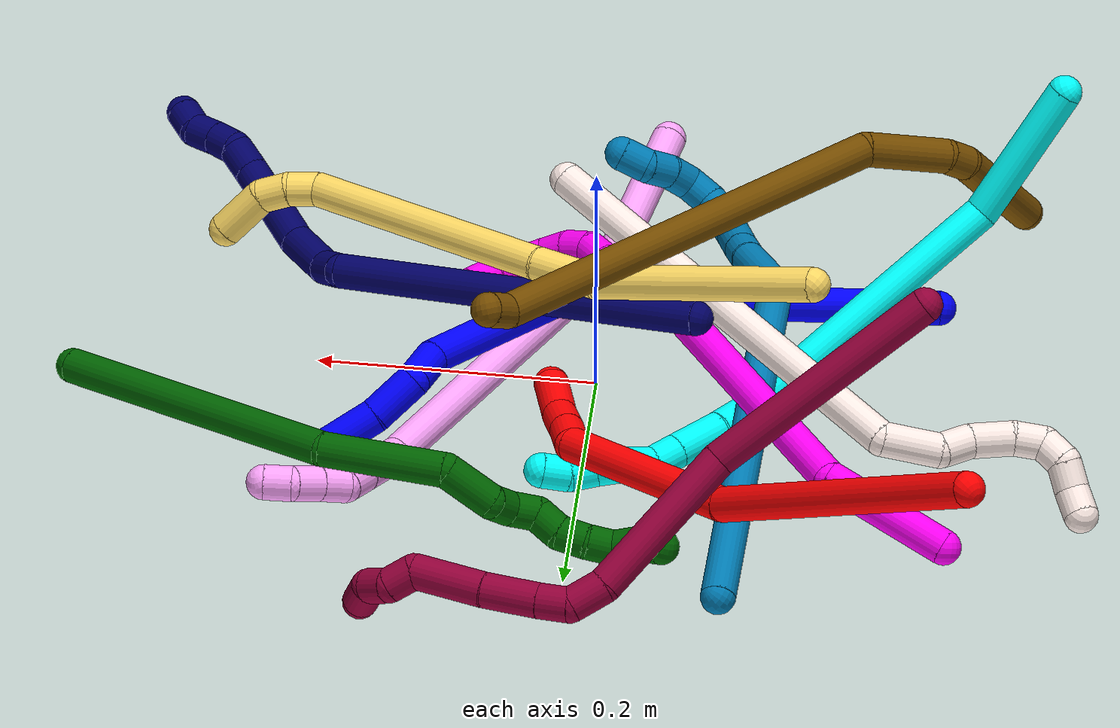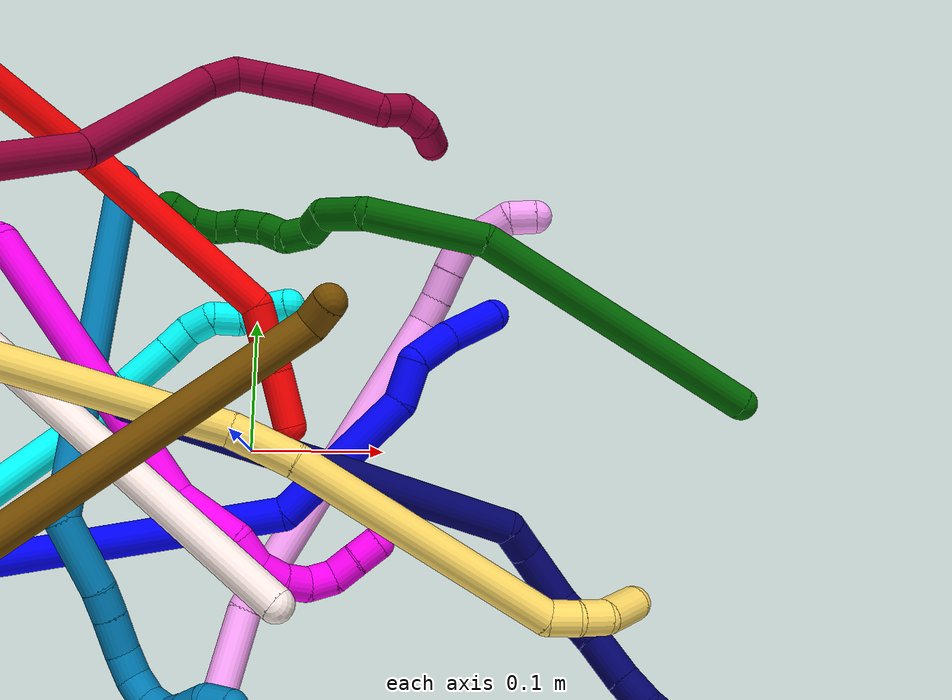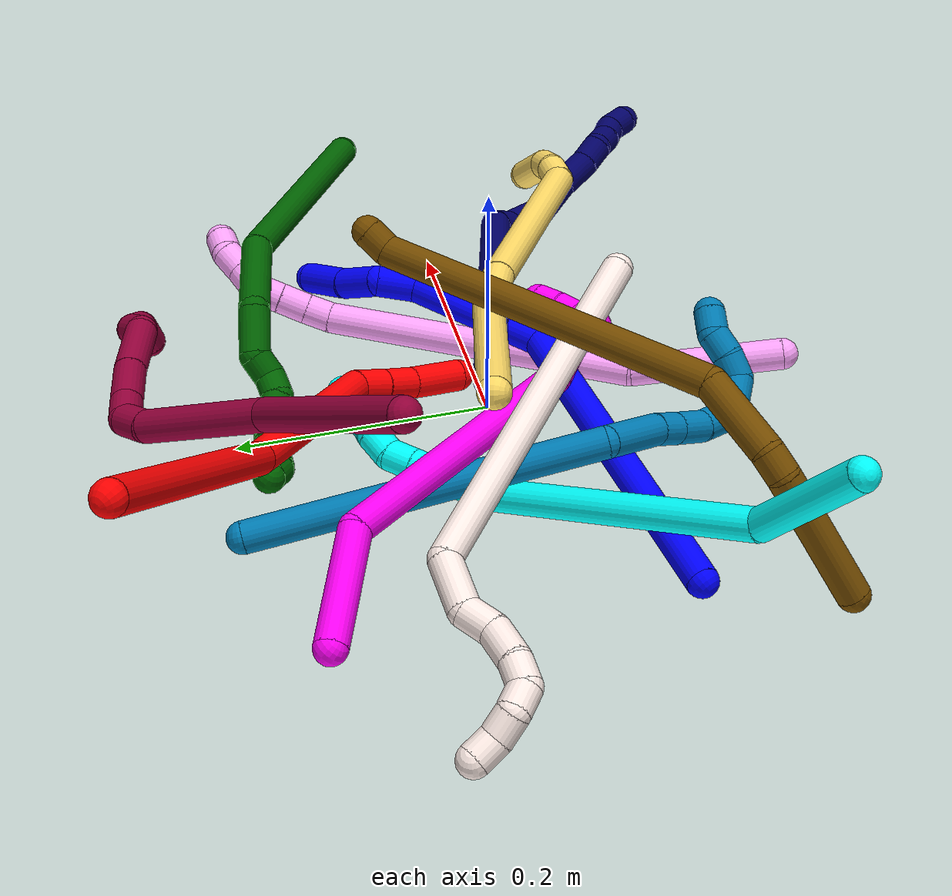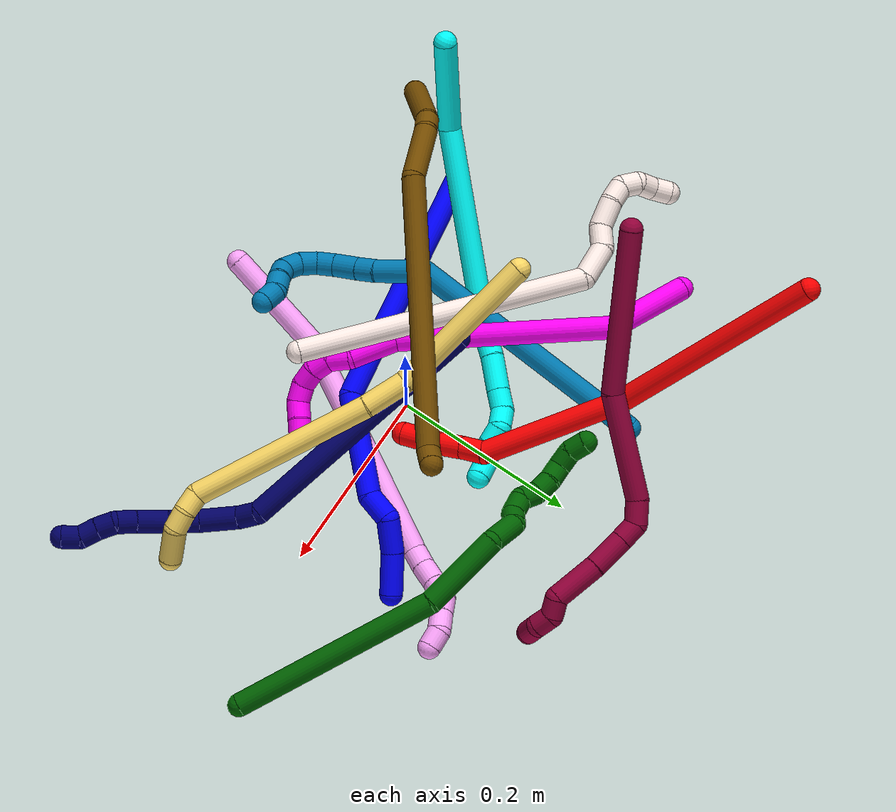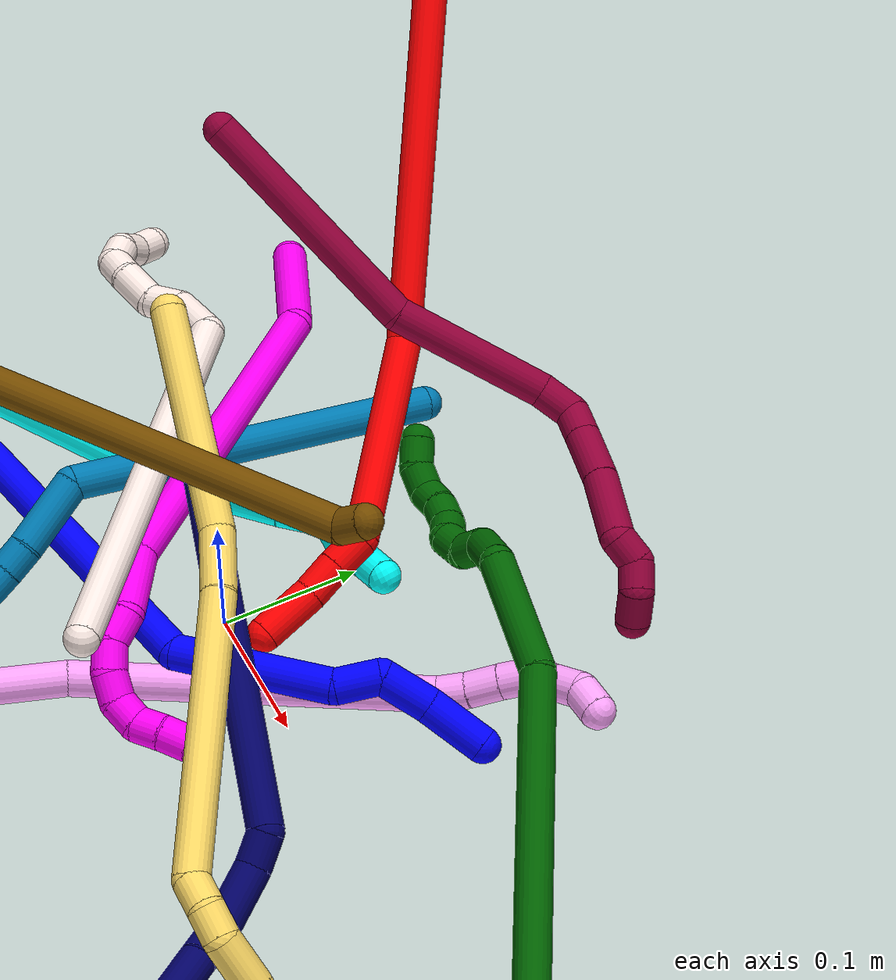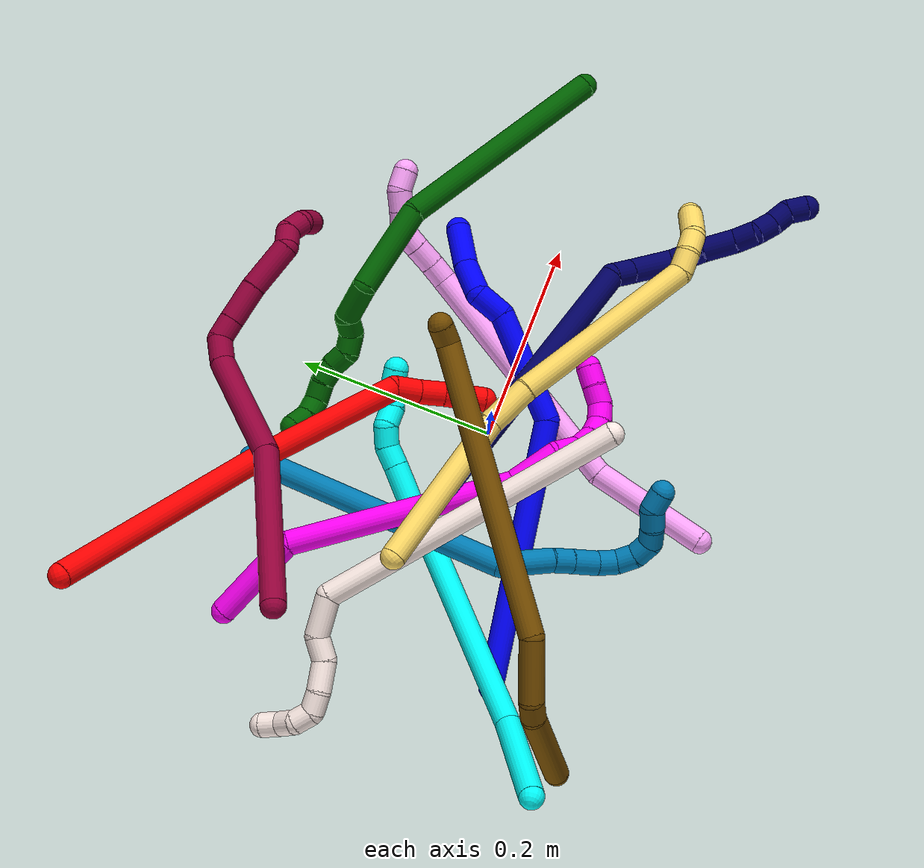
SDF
<sdf version="1.7">
 <world name="default">
  <plugin name="TubeGeneratorPlugin" filename="libtube_generator_plugin.so"/>
  <model name="photoneo_s_sensor">
   <static>1</static>
   <pose>0 0 2 1.57079 1.57079 3.14159</pose>
   <link name="link">
    <inertial><mass>0.1</mass></inertial>
    <sensor name="sensor" type="depth">
     <update_rate>30</update_rate>
     <camera>
      <horizontal_fov>1.22</horizontal_fov>
      <image><width>1920</width><height>1200</height><format>B8G8R8</format></image>
      <clip><near>0.1</near><far>4</far></clip>
      <depth_camera><output>points</output></depth_camera>
     </camera>
     <plugin name="camera_plugin" filename="libgazebo_ros_depth_camera.so">
      <baseline>0.2</baseline>
      <alwaysOn>1</alwaysOn>
      <updateRate>0.0</updateRate>
      <cameraName>camera_ir</cameraName>
      <imageTopicName>/camera/color/image_raw</imageTopicName>
      <cameraInfoTopicName>/camera/color/camera_info</cameraInfoTopicName>
      <depthImageTopicName>/camera/depth/image_raw</depthImageTopicName>
      <depthImageCameraInfoTopicName>/camera/depth/camera_info</depthImageCameraInfoTopicName>
      <pointCloudTopicName>/camera/depth/points</pointCloudTopicName>
      <frameName>fr_optical</frameName>
      <pointCloudCutoff>0.1</pointCloudCutoff>
      <pointCloudCutoffMax>2.0</pointCloudCutoffMax>
      <distortionK1>0</distortionK1>
      <distortionK2>0</distortionK2>
      <distortionK3>0</distortionK3>
      <distortionT1>0</distortionT1>
      <distortionT2>0</distortionT2>
      <CxPrime>0</CxPrime>
      <Cx>0</Cx>
      <Cy>0</Cy>
      <focalLength>0</focalLength>
      <hackBaseline>0</hackBaseline>
     </plugin>
    </sensor>
   </link>
  </model>
  <gravity>0 0 -9.8</gravity>
  <magnetic_field>6e-06 2.3e-05 -4.2e-05</magnetic_field>
  <atmosphere type="adiabatic"/>
  <physics name="default_physics" default="0" type="ode">
   <max_step_size>0.003</max_step_size>
   <real_time_factor>1</real_time_factor>
   <real_time_update_rate>1000</real_time_update_rate>
   <max_contacts>10000</max_contacts>
   <ode>
    <solver>
     <type>quick</type>
     <iters>100</iters>
     <sor>1.3</sor>
     <use_dynamic_moi_rescaling>0</use_dynamic_moi_rescaling>
    </solver>
    <constraints>
     <contact_max_correcting_vel>0</contact_max_correcting_vel>
     <contact_surface_layer>0.001</contact_surface_layer>
     <cfm>0</cfm>
     <erp>0.2</erp>
    </constraints>
   </ode>
  </physics>
  <scene><ambient>0.4 0.4 0.4 1</ambient><background>0.7 0.7 0.7 1</background><shadows>0</shadows></scene>
  <audio><device>default</device></audio>
  <spherical_coordinates>
   <surface_model>EARTH_WGS84</surface_model>
   <latitude_deg>0</latitude_deg>
   <longitude_deg>0</longitude_deg>
   <elevation>0</elevation>
   <heading_deg>0</heading_deg>
  </spherical_coordinates>
  <model name="bin">
   <static>1</static>
   <link name="bottom">
    <collision name="collision-bottom">
     <pose>0 0 -0.01 0 -0 0</pose>
     <geometry><box><size>0.8 0.6 0.02</size></box></geometry>
     <surface>
      <friction><ode><mu>100</mu><mu2>100</mu2></ode></friction>
      <contact><collide_bitmask>65535</collide_bitmask></contact>
     </surface>
    </collision>
   </link>
   <link name="west_wall">
    <collision name="collision-west_wall">
     <pose>-0.41 0 0.1 0 -0 0</pose>
     <geometry><box><size>0.02 0.6 0.2</size></box></geometry>
     <surface>
      <friction><ode><mu>100</mu><mu2>100</mu2></ode></friction>
      <contact><collide_bitmask>65535</collide_bitmask></contact>
     </surface>
    </collision>
   </link>
   <link name="east_wall">
    <collision name="collision-east_wall">
     <pose>0.41 0 0.1 0 -0 0</pose>
     <geometry><box><size>0.02 0.6 0.2</size></box></geometry>
     <surface>
      <friction><ode><mu>100</mu><mu2>100</mu2></ode></friction>
      <contact><collide_bitmask>65535</collide_bitmask></contact>
     </surface>
    </collision>
   </link>
   <link name="south_wall">
    <collision name="collision-south_wall">
     <pose>0 -0.31 0.1 0 -0 0</pose>
     <geometry><box><size>0.8 0.02 0.2</size></box></geometry>
     <surface>
      <friction><ode><mu>100</mu><mu2>100</mu2></ode></friction>
      <contact><collide_bitmask>65535</collide_bitmask></contact>
     </surface>
    </collision>
   </link>
   <link name="north_wall">
    <collision name="collision-north_wall">
     <pose>0 0.31 0.1 0 -0 0</pose>
     <geometry><box><size>0.8 0.02 0.2</size></box></geometry>
     <surface>
      <friction><ode><mu>100</mu><mu2>100</mu2></ode></friction>
      <contact><collide_bitmask>65535</collide_bitmask></contact>
     </surface>
    </collision>
   </link>
  </model>
  <model name="1">
   <static>0</static>
   <link name="1">
    <collision name="collision-cylinder-e_1_1_4">
     <pose>-0.035363 0.040154 -0.124892 -2.83052 -0.263304 1.40258</pose>
     <geometry><cylinder><radius>0.0125</radius><length>0.271742</length></cylinder></geometry>
     <surface>
      <friction><ode><mu>1.16</mu><mu2>1.16</mu2><slip1>0</slip1><slip2>0</slip2></ode></friction>
      <contact><ode><kp>1e+06</kp><kd>1</kd><max_vel>0</max_vel><min_depth>0.001</min_depth></ode></contact>
     </surface>
    </collision>
    <visual name="visual-cylinder-e_1_1_4">
     <pose>-0.035363 0.040154 -0.124892 -2.83052 -0.263304 1.40258</pose>
     <geometry><cylinder><radius>0.0125</radius><length>0.271742</length></cylinder></geometry>
     <material><ambient>0 0 1 1</ambient></material>
    </visual>
    <collision name="collision-cylinder-e_2_4_5">
     <pose>-0.051179 0.097199 -0.301066 -2.82341 0.347371 -1.66008</pose>
     <geometry><cylinder><radius>0.0125</radius><length>0.114843</length></cylinder></geometry>
     <surface>
      <friction><ode><mu>1.16</mu><mu2>1.16</mu2><slip1>0</slip1><slip2>0</slip2></ode></friction>
      <contact><ode><kp>1e+06</kp><kd>1</kd><max_vel>0</max_vel><min_depth>0.001</min_depth></ode></contact>
     </surface>
    </collision>
    <visual name="visual-cylinder-e_2_4_5">
     <pose>-0.051179 0.097199 -0.301066 -2.82341 0.347371 -1.66008</pose>
     <geometry><cylinder><radius>0.0125</radius><length>0.114843</length></cylinder></geometry>
     <material><ambient>0 0 1 1</ambient></material>
    </visual>
    <collision name="collision-cylinder-e_3_5_6">
     <pose>-0.020027 0.116161 -0.363003 -2.94956 0.818742 -2.70473</pose>
     <geometry><cylinder><radius>0.0125</radius><length>0.03178</length></cylinder></geometry>
     <surface>
      <friction><ode><mu>1.16</mu><mu2>1.16</mu2><slip1>0</slip1><slip2>0</slip2></ode></friction>
      <contact><ode><kp>1e+06</kp><kd>1</kd><max_vel>0</max_vel><min_depth>0.001</min_depth></ode></contact>
     </surface>
    </collision>
    <visual name="visual-cylinder-e_3_5_6">
     <pose>-0.020027 0.116161 -0.363003 -2.94956 0.818742 -2.70473</pose>
     <geometry><cylinder><radius>0.0125</radius><length>0.03178</length></cylinder></geometry>
     <material><ambient>0 0 1 1</ambient></material>
    </visual>
    <collision name="collision-cylinder-e_4_6_7">
     <pose>-0.003386 0.131756 -0.385176 -2.27628 0.276301 -0.58484</pose>
     <geometry><cylinder><radius>0.0125</radius><length>0.036928</length></cylinder></geometry>
     <surface>
      <friction><ode><mu>1.16</mu><mu2>1.16</mu2><slip1>0</slip1><slip2>0</slip2></ode></friction>
      <contact><ode><kp>1e+06</kp><kd>1</kd><max_vel>0</max_vel><min_depth>0.001</min_depth></ode></contact>
     </surface>
    </collision>
    <visual name="visual-cylinder-e_4_6_7">
     <pose>-0.003386 0.131756 -0.385176 -2.27628 0.276301 -0.58484</pose>
     <geometry><cylinder><radius>0.0125</radius><length>0.036928</length></cylinder></geometry>
     <material><ambient>0 0 1 1</ambient></material>
    </visual>
    <collision name="collision-cylinder-e_5_7_2">
     <pose>0.004295 0.160531 -0.412822 -2.38412 0.118555 -0.296084</pose>
     <geometry><cylinder><radius>0.0125</radius><length>0.044707</length></cylinder></geometry>
     <surface>
      <friction><ode><mu>1.16</mu><mu2>1.16</mu2><slip1>0</slip1><slip2>0</slip2></ode></friction>
      <contact><ode><kp>1e+06</kp><kd>1</kd><max_vel>0</max_vel><min_depth>0.001</min_depth></ode></contact>
     </surface>
    </collision>
    <visual name="visual-cylinder-e_5_7_2">
     <pose>0.004295 0.160531 -0.412822 -2.38412 0.118555 -0.296084</pose>
     <geometry><cylinder><radius>0.0125</radius><length>0.044707</length></cylinder></geometry>
     <material><ambient>0 0 1 1</ambient></material>
    </visual>
    <collision name="collision-sphere-2">
     <pose>0.006939 0.175782 -0.42895 0 -0 0</pose>
     <geometry><sphere><radius>0.0125</radius></sphere></geometry>
     <surface>
      <friction><ode><mu>1.16</mu><mu2>1.16</mu2><slip1>0</slip1><slip2>0</slip2></ode></friction>
      <contact><ode><kp>1e+06</kp><kd>1</kd><max_vel>0</max_vel><min_depth>0.001</min_depth></ode></contact>
     </surface>
    </collision>
    <visual name="visual-sphere-2">
     <pose>0.006939 0.175782 -0.42895 0 -0 0</pose>
     <geometry><sphere><radius>0.0125</radius></sphere></geometry>
     <material><ambient>0 0 1 1</ambient></material>
    </visual>
    <collision name="collision-sphere-7">
     <pose>0.001651 0.14528 -0.396694 0 -0 0</pose>
     <geometry><sphere><radius>0.0125</radius></sphere></geometry>
     <surface>
      <friction><ode><mu>1.16</mu><mu2>1.16</mu2><slip1>0</slip1><slip2>0</slip2></ode></friction>
      <contact><ode><kp>1e+06</kp><kd>1</kd><max_vel>0</max_vel><min_depth>0.001</min_depth></ode></contact>
     </surface>
    </collision>
    <visual name="visual-sphere-7">
     <pose>0.001651 0.14528 -0.396694 0 -0 0</pose>
     <geometry><sphere><radius>0.0125</radius></sphere></geometry>
     <material><ambient>0 0 1 1</ambient></material>
    </visual>
    <collision name="collision-sphere-6">
     <pose>-0.008423 0.118233 -0.373658 0 -0 0</pose>
     <geometry><sphere><radius>0.0125</radius></sphere></geometry>
     <surface>
      <friction><ode><mu>1.16</mu><mu2>1.16</mu2><slip1>0</slip1><slip2>0</slip2></ode></friction>
      <contact><ode><kp>1e+06</kp><kd>1</kd><max_vel>0</max_vel><min_depth>0.001</min_depth></ode></contact>
     </surface>
    </collision>
    <visual name="visual-sphere-6">
     <pose>-0.008423 0.118233 -0.373658 0 -0 0</pose>
     <geometry><sphere><radius>0.0125</radius></sphere></geometry>
     <material><ambient>0 0 1 1</ambient></material>
    </visual>
    <collision name="collision-sphere-5">
     <pose>-0.031631 0.114089 -0.352347 0 -0 0</pose>
     <geometry><sphere><radius>0.0125</radius></sphere></geometry>
     <surface>
      <friction><ode><mu>1.16</mu><mu2>1.16</mu2><slip1>0</slip1><slip2>0</slip2></ode></friction>
      <contact><ode><kp>1e+06</kp><kd>1</kd><max_vel>0</max_vel><min_depth>0.001</min_depth></ode></contact>
     </surface>
    </collision>
    <visual name="visual-sphere-5">
     <pose>-0.031631 0.114089 -0.352347 0 -0 0</pose>
     <geometry><sphere><radius>0.0125</radius></sphere></geometry>
     <material><ambient>0 0 1 1</ambient></material>
    </visual>
    <collision name="collision-sphere-1">
     <geometry><sphere><radius>0.0125</radius></sphere></geometry>
     <surface>
      <friction><ode><mu>1.16</mu><mu2>1.16</mu2><slip1>0</slip1><slip2>0</slip2></ode></friction>
      <contact><ode><kp>1e+06</kp><kd>1</kd><max_vel>0</max_vel><min_depth>0.001</min_depth></ode></contact>
     </surface>
    </collision>
    <visual name="visual-sphere-1">
     <geometry><sphere><radius>0.0125</radius></sphere></geometry>
     <material><ambient>0 0 1 1</ambient></material>
    </visual>
    <collision name="collision-sphere-4">
     <pose>-0.070727 0.080308 -0.249784 0 -0 0</pose>
     <geometry><sphere><radius>0.0125</radius></sphere></geometry>
     <surface>
      <friction><ode><mu>1.16</mu><mu2>1.16</mu2><slip1>0</slip1><slip2>0</slip2></ode></friction>
      <contact><ode><kp>1e+06</kp><kd>1</kd><max_vel>0</max_vel><min_depth>0.001</min_depth></ode></contact>
     </surface>
    </collision>
    <visual name="visual-sphere-4">
     <pose>-0.070727 0.080308 -0.249784 0 -0 0</pose>
     <geometry><sphere><radius>0.0125</radius></sphere></geometry>
     <material><ambient>0 0 1 1</ambient></material>
    </visual>
    <inertial>
     <pose>-0.032114 0.075616 -0.22546 0 -0 0</pose>
     <mass>0.5</mass>
     <inertia>
      <ixx>0.001745</ixx>
      <ixy>0</ixy>
      <ixz>0</ixz>
      <iyy>0.00137</iyy>
      <iyz>0</iyz>
      <izz>-0.000192</izz>
     </inertia>
    </inertial>
   </link>
   <pose>-0.235937 -0.094572 0.011994 -1.966 -0.00429 1.99972</pose>
  </model>
  <model name="2">
   <static>0</static>
   <link name="2">
    <collision name="collision-cylinder-e_1_1_4">
     <pose>0.005366 -0.071819 -0.102553 2.53066 0.042832 0.135643</pose>
     <geometry><cylinder><radius>0.0125</radius><length>0.250631</length></cylinder></geometry>
     <surface>
      <friction><ode><mu>1.16</mu><mu2>1.16</mu2><slip1>0</slip1><slip2>0</slip2></ode></friction>
      <contact><ode><kp>1e+06</kp><kd>1</kd><max_vel>0</max_vel><min_depth>0.001</min_depth></ode></contact>
     </surface>
    </collision>
    <visual name="visual-cylinder-e_1_1_4">
     <pose>0.005366 -0.071819 -0.102553 2.53066 0.042832 0.135643</pose>
     <geometry><cylinder><radius>0.0125</radius><length>0.250631</length></cylinder></geometry>
     <material><ambient>1 0 0 1</ambient></material>
    </visual>
    <collision name="collision-cylinder-e_2_4_5">
     <pose>0.008949 -0.165995 -0.279182 2.84848 -0.023033 -0.155726</pose>
     <geometry><cylinder><radius>0.0125</radius><length>0.154792</length></cylinder></geometry>
     <surface>
      <friction><ode><mu>1.16</mu><mu2>1.16</mu2><slip1>0</slip1><slip2>0</slip2></ode></friction>
      <contact><ode><kp>1e+06</kp><kd>1</kd><max_vel>0</max_vel><min_depth>0.001</min_depth></ode></contact>
     </surface>
    </collision>
    <visual name="visual-cylinder-e_2_4_5">
     <pose>0.008949 -0.165995 -0.279182 2.84848 -0.023033 -0.155726</pose>
     <geometry><cylinder><radius>0.0125</radius><length>0.154792</length></cylinder></geometry>
     <material><ambient>1 0 0 1</ambient></material>
    </visual>
    <collision name="collision-cylinder-e_3_5_6">
     <pose>0.013792 -0.189385 -0.364147 3.04694 0.54458 2.80555</pose>
     <geometry><cylinder><radius>0.0125</radius><length>0.025577</length></cylinder></geometry>
     <surface>
      <friction><ode><mu>1.16</mu><mu2>1.16</mu2><slip1>0</slip1><slip2>0</slip2></ode></friction>
      <contact><ode><kp>1e+06</kp><kd>1</kd><max_vel>0</max_vel><min_depth>0.001</min_depth></ode></contact>
     </surface>
    </collision>
    <visual name="visual-cylinder-e_3_5_6">
     <pose>0.013792 -0.189385 -0.364147 3.04694 0.54458 2.80555</pose>
     <geometry><cylinder><radius>0.0125</radius><length>0.025577</length></cylinder></geometry>
     <material><ambient>1 0 0 1</ambient></material>
    </visual>
    <collision name="collision-cylinder-e_4_6_7">
     <pose>0.026655 -0.191814 -0.386681 3.02241 0.488835 2.67197</pose>
     <geometry><cylinder><radius>0.0125</radius><length>0.026566</length></cylinder></geometry>
     <surface>
      <friction><ode><mu>1.16</mu><mu2>1.16</mu2><slip1>0</slip1><slip2>0</slip2></ode></friction>
      <contact><ode><kp>1e+06</kp><kd>1</kd><max_vel>0</max_vel><min_depth>0.001</min_depth></ode></contact>
     </surface>
    </collision>
    <visual name="visual-cylinder-e_4_6_7">
     <pose>0.026655 -0.191814 -0.386681 3.02241 0.488835 2.67197</pose>
     <geometry><cylinder><radius>0.0125</radius><length>0.026566</length></cylinder></geometry>
     <material><ambient>1 0 0 1</ambient></material>
    </visual>
    <collision name="collision-cylinder-e_5_7_2">
     <pose>0.042968 -0.192226 -0.416971 -3.08896 0.494849 -2.93394</pose>
     <geometry><cylinder><radius>0.0125</radius><length>0.042433</length></cylinder></geometry>
     <surface>
      <friction><ode><mu>1.16</mu><mu2>1.16</mu2><slip1>0</slip1><slip2>0</slip2></ode></friction>
      <contact><ode><kp>1e+06</kp><kd>1</kd><max_vel>0</max_vel><min_depth>0.001</min_depth></ode></contact>
     </surface>
    </collision>
    <visual name="visual-cylinder-e_5_7_2">
     <pose>0.042968 -0.192226 -0.416971 -3.08896 0.494849 -2.93394</pose>
     <geometry><cylinder><radius>0.0125</radius><length>0.042433</length></cylinder></geometry>
     <material><ambient>1 0 0 1</ambient></material>
    </visual>
    <collision name="collision-sphere-2">
     <pose>0.053044 -0.191243 -0.435617 0 -0 0</pose>
     <geometry><sphere><radius>0.0125</radius></sphere></geometry>
     <surface>
      <friction><ode><mu>1.16</mu><mu2>1.16</mu2><slip1>0</slip1><slip2>0</slip2></ode></friction>
      <contact><ode><kp>1e+06</kp><kd>1</kd><max_vel>0</max_vel><min_depth>0.001</min_depth></ode></contact>
     </surface>
    </collision>
    <visual name="visual-sphere-2">
     <pose>0.053044 -0.191243 -0.435617 0 -0 0</pose>
     <geometry><sphere><radius>0.0125</radius></sphere></geometry>
     <material><ambient>1 0 0 1</ambient></material>
    </visual>
    <collision name="collision-sphere-7">
     <pose>0.032893 -0.193208 -0.398325 0 -0 0</pose>
     <geometry><sphere><radius>0.0125</radius></sphere></geometry>
     <surface>
      <friction><ode><mu>1.16</mu><mu2>1.16</mu2><slip1>0</slip1><slip2>0</slip2></ode></friction>
      <contact><ode><kp>1e+06</kp><kd>1</kd><max_vel>0</max_vel><min_depth>0.001</min_depth></ode></contact>
     </surface>
    </collision>
    <visual name="visual-sphere-7">
     <pose>0.032893 -0.193208 -0.398325 0 -0 0</pose>
     <geometry><sphere><radius>0.0125</radius></sphere></geometry>
     <material><ambient>1 0 0 1</ambient></material>
    </visual>
    <collision name="collision-sphere-6">
     <pose>0.020417 -0.190419 -0.375037 0 -0 0</pose>
     <geometry><sphere><radius>0.0125</radius></sphere></geometry>
     <surface>
      <friction><ode><mu>1.16</mu><mu2>1.16</mu2><slip1>0</slip1><slip2>0</slip2></ode></friction>
      <contact><ode><kp>1e+06</kp><kd>1</kd><max_vel>0</max_vel><min_depth>0.001</min_depth></ode></contact>
     </surface>
    </collision>
    <visual name="visual-sphere-6">
     <pose>0.020417 -0.190419 -0.375037 0 -0 0</pose>
     <geometry><sphere><radius>0.0125</radius></sphere></geometry>
     <material><ambient>1 0 0 1</ambient></material>
    </visual>
    <collision name="collision-sphere-5">
     <pose>0.007167 -0.188351 -0.353258 0 -0 0</pose>
     <geometry><sphere><radius>0.0125</radius></sphere></geometry>
     <surface>
      <friction><ode><mu>1.16</mu><mu2>1.16</mu2><slip1>0</slip1><slip2>0</slip2></ode></friction>
      <contact><ode><kp>1e+06</kp><kd>1</kd><max_vel>0</max_vel><min_depth>0.001</min_depth></ode></contact>
     </surface>
    </collision>
    <visual name="visual-sphere-5">
     <pose>0.007167 -0.188351 -0.353258 0 -0 0</pose>
     <geometry><sphere><radius>0.0125</radius></sphere></geometry>
     <material><ambient>1 0 0 1</ambient></material>
    </visual>
    <collision name="collision-sphere-1">
     <geometry><sphere><radius>0.0125</radius></sphere></geometry>
     <surface>
      <friction><ode><mu>1.16</mu><mu2>1.16</mu2><slip1>0</slip1><slip2>0</slip2></ode></friction>
      <contact><ode><kp>1e+06</kp><kd>1</kd><max_vel>0</max_vel><min_depth>0.001</min_depth></ode></contact>
     </surface>
    </collision>
    <visual name="visual-sphere-1">
     <geometry><sphere><radius>0.0125</radius></sphere></geometry>
     <material><ambient>1 0 0 1</ambient></material>
    </visual>
    <collision name="collision-sphere-4">
     <pose>0.010732 -0.143639 -0.205107 0 -0 0</pose>
     <geometry><sphere><radius>0.0125</radius></sphere></geometry>
     <surface>
      <friction><ode><mu>1.16</mu><mu2>1.16</mu2><slip1>0</slip1><slip2>0</slip2></ode></friction>
      <contact><ode><kp>1e+06</kp><kd>1</kd><max_vel>0</max_vel><min_depth>0.001</min_depth></ode></contact>
     </surface>
    </collision>
    <visual name="visual-sphere-4">
     <pose>0.010732 -0.143639 -0.205107 0 -0 0</pose>
     <geometry><sphere><radius>0.0125</radius></sphere></geometry>
     <material><ambient>1 0 0 1</ambient></material>
    </visual>
    <inertial>
     <pose>0.011229 -0.123583 -0.212396 0 -0 0</pose>
     <mass>0.5</mass>
     <inertia>
      <ixx>0.001743</ixx>
      <ixy>0</ixy>
      <ixz>0</ixz>
      <iyy>-0.001238</iyy>
      <iyz>0</iyz>
      <izz>0.000759</izz>
     </inertia>
    </inertial>
   </link>
   <pose>-0.283828 0.306736 0.227749 1.51742 0.461636 -2.42924</pose>
  </model>
  <model name="3">
   <static>0</static>
   <link name="3">
    <collision name="collision-cylinder-e_1_1_4">
     <pose>-0.016503 0.016535 -0.048073 -2.81031 -0.313898 1.51597</pose>
     <geometry><cylinder><radius>0.0125</radius><length>0.106898</length></cylinder></geometry>
     <surface>
      <friction><ode><mu>1.16</mu><mu2>1.16</mu2><slip1>0</slip1><slip2>0</slip2></ode></friction>
      <contact><ode><kp>1e+06</kp><kd>1</kd><max_vel>0</max_vel><min_depth>0.001</min_depth></ode></contact>
     </surface>
    </collision>
    <visual name="visual-cylinder-e_1_1_4">
     <pose>-0.016503 0.016535 -0.048073 -2.81031 -0.313898 1.51597</pose>
     <geometry><cylinder><radius>0.0125</radius><length>0.106898</length></cylinder></geometry>
     <material><ambient>0.003922 1 0.996078 1</ambient></material>
    </visual>
    <collision name="collision-cylinder-e_2_4_5">
     <pose>-0.013756 0.097436 -0.185815 -2.51902 0.17267 -0.525558</pose>
     <geometry><cylinder><radius>0.0125</radius><length>0.22409</length></cylinder></geometry>
     <surface>
      <friction><ode><mu>1.16</mu><mu2>1.16</mu2><slip1>0</slip1><slip2>0</slip2></ode></friction>
      <contact><ode><kp>1e+06</kp><kd>1</kd><max_vel>0</max_vel><min_depth>0.001</min_depth></ode></contact>
     </surface>
    </collision>
    <visual name="visual-cylinder-e_2_4_5">
     <pose>-0.013756 0.097436 -0.185815 -2.51902 0.17267 -0.525558</pose>
     <geometry><cylinder><radius>0.0125</radius><length>0.22409</length></cylinder></geometry>
     <material><ambient>0.003922 1 0.996078 1</ambient></material>
    </visual>
    <collision name="collision-cylinder-e_3_5_6">
     <pose>0.011627 0.17106 -0.282894 -2.24568 0.477213 -0.937163</pose>
     <geometry><cylinder><radius>0.0125</radius><length>0.026702</length></cylinder></geometry>
     <surface>
      <friction><ode><mu>1.16</mu><mu2>1.16</mu2><slip1>0</slip1><slip2>0</slip2></ode></friction>
      <contact><ode><kp>1e+06</kp><kd>1</kd><max_vel>0</max_vel><min_depth>0.001</min_depth></ode></contact>
     </surface>
    </collision>
    <visual name="visual-cylinder-e_3_5_6">
     <pose>0.011627 0.17106 -0.282894 -2.24568 0.477213 -0.937163</pose>
     <geometry><cylinder><radius>0.0125</radius><length>0.026702</length></cylinder></geometry>
     <material><ambient>0.003922 1 0.996078 1</ambient></material>
    </visual>
    <collision name="collision-cylinder-e_4_6_7">
     <pose>0.026614 0.19211 -0.302884 -2.38857 0.47444 -1.09768</pose>
     <geometry><cylinder><radius>0.0125</radius><length>0.038765</length></cylinder></geometry>
     <surface>
      <friction><ode><mu>1.16</mu><mu2>1.16</mu2><slip1>0</slip1><slip2>0</slip2></ode></friction>
      <contact><ode><kp>1e+06</kp><kd>1</kd><max_vel>0</max_vel><min_depth>0.001</min_depth></ode></contact>
     </surface>
    </collision>
    <visual name="visual-cylinder-e_4_6_7">
     <pose>0.026614 0.19211 -0.302884 -2.38857 0.47444 -1.09768</pose>
     <geometry><cylinder><radius>0.0125</radius><length>0.038765</length></cylinder></geometry>
     <material><ambient>0.003922 1 0.996078 1</ambient></material>
    </visual>
    <collision name="collision-cylinder-e_5_7_8">
     <pose>0.040617 0.21088 -0.322135 -2.33364 0.48992 -1.05829</pose>
     <geometry><cylinder><radius>0.0125</radius><length>0.021883</length></cylinder></geometry>
     <surface>
      <friction><ode><mu>1.16</mu><mu2>1.16</mu2><slip1>0</slip1><slip2>0</slip2></ode></friction>
      <contact><ode><kp>1e+06</kp><kd>1</kd><max_vel>0</max_vel><min_depth>0.001</min_depth></ode></contact>
     </surface>
    </collision>
    <visual name="visual-cylinder-e_5_7_8">
     <pose>0.040617 0.21088 -0.322135 -2.33364 0.48992 -1.05829</pose>
     <geometry><cylinder><radius>0.0125</radius><length>0.021883</length></cylinder></geometry>
     <material><ambient>0.003922 1 0.996078 1</ambient></material>
    </visual>
    <collision name="collision-cylinder-e_6_8_9">
     <pose>0.053761 0.221195 -0.334929 -2.64269 0.853522 -2.12022</pose>
     <geometry><cylinder><radius>0.0125</radius><length>0.021218</length></cylinder></geometry>
     <surface>
      <friction><ode><mu>1.16</mu><mu2>1.16</mu2><slip1>0</slip1><slip2>0</slip2></ode></friction>
      <contact><ode><kp>1e+06</kp><kd>1</kd><max_vel>0</max_vel><min_depth>0.001</min_depth></ode></contact>
     </surface>
    </collision>
    <visual name="visual-cylinder-e_6_8_9">
     <pose>0.053761 0.221195 -0.334929 -2.64269 0.853522 -2.12022</pose>
     <geometry><cylinder><radius>0.0125</radius><length>0.021218</length></cylinder></geometry>
     <material><ambient>0.003922 1 0.996078 1</ambient></material>
    </visual>
    <collision name="collision-cylinder-e_7_9_10">
     <pose>0.065332 0.223657 -0.350395 3.04822 0.364109 2.64451</pose>
     <geometry><cylinder><radius>0.0125</radius><length>0.020083</length></cylinder></geometry>
     <surface>
      <friction><ode><mu>1.16</mu><mu2>1.16</mu2><slip1>0</slip1><slip2>0</slip2></ode></friction>
      <contact><ode><kp>1e+06</kp><kd>1</kd><max_vel>0</max_vel><min_depth>0.001</min_depth></ode></contact>
     </surface>
    </collision>
    <visual name="visual-cylinder-e_7_9_10">
     <pose>0.065332 0.223657 -0.350395 3.04822 0.364109 2.64451</pose>
     <geometry><cylinder><radius>0.0125</radius><length>0.020083</length></cylinder></geometry>
     <material><ambient>0.003922 1 0.996078 1</ambient></material>
    </visual>
    <collision name="collision-cylinder-e_8_10_11">
     <pose>0.074689 0.225753 -0.367571 -2.7791 0.604039 -2.07817</pose>
     <geometry><cylinder><radius>0.0125</radius><length>0.020358</length></cylinder></geometry>
     <surface>
      <friction><ode><mu>1.16</mu><mu2>1.16</mu2><slip1>0</slip1><slip2>0</slip2></ode></friction>
      <contact><ode><kp>1e+06</kp><kd>1</kd><max_vel>0</max_vel><min_depth>0.001</min_depth></ode></contact>
     </surface>
    </collision>
    <visual name="visual-cylinder-e_8_10_11">
     <pose>0.074689 0.225753 -0.367571 -2.7791 0.604039 -2.07817</pose>
     <geometry><cylinder><radius>0.0125</radius><length>0.020358</length></cylinder></geometry>
     <material><ambient>0.003922 1 0.996078 1</ambient></material>
    </visual>
    <collision name="collision-cylinder-e_9_11_2">
     <pose>0.088096 0.229239 -0.381856 -3.06186 0.867004 -2.96968</pose>
     <geometry><cylinder><radius>0.0125</radius><length>0.020005</length></cylinder></geometry>
     <surface>
      <friction><ode><mu>1.16</mu><mu2>1.16</mu2><slip1>0</slip1><slip2>0</slip2></ode></friction>
      <contact><ode><kp>1e+06</kp><kd>1</kd><max_vel>0</max_vel><min_depth>0.001</min_depth></ode></contact>
     </surface>
    </collision>
    <visual name="visual-cylinder-e_9_11_2">
     <pose>0.088096 0.229239 -0.381856 -3.06186 0.867004 -2.96968</pose>
     <geometry><cylinder><radius>0.0125</radius><length>0.020005</length></cylinder></geometry>
     <material><ambient>0.003922 1 0.996078 1</ambient></material>
    </visual>
    <collision name="collision-sphere-2">
     <pose>0.095722 0.229755 -0.388308 0 -0 0</pose>
     <geometry><sphere><radius>0.0125</radius></sphere></geometry>
     <surface>
      <friction><ode><mu>1.16</mu><mu2>1.16</mu2><slip1>0</slip1><slip2>0</slip2></ode></friction>
      <contact><ode><kp>1e+06</kp><kd>1</kd><max_vel>0</max_vel><min_depth>0.001</min_depth></ode></contact>
     </surface>
    </collision>
    <visual name="visual-sphere-2">
     <pose>0.095722 0.229755 -0.388308 0 -0 0</pose>
     <geometry><sphere><radius>0.0125</radius></sphere></geometry>
     <material><ambient>0.003922 1 0.996078 1</ambient></material>
    </visual>
    <collision name="collision-sphere-11">
     <pose>0.08047 0.228724 -0.375404 0 -0 0</pose>
     <geometry><sphere><radius>0.0125</radius></sphere></geometry>
     <surface>
      <friction><ode><mu>1.16</mu><mu2>1.16</mu2><slip1>0</slip1><slip2>0</slip2></ode></friction>
      <contact><ode><kp>1e+06</kp><kd>1</kd><max_vel>0</max_vel><min_depth>0.001</min_depth></ode></contact>
     </surface>
    </collision>
    <visual name="visual-sphere-11">
     <pose>0.08047 0.228724 -0.375404 0 -0 0</pose>
     <geometry><sphere><radius>0.0125</radius></sphere></geometry>
     <material><ambient>0.003922 1 0.996078 1</ambient></material>
    </visual>
    <collision name="collision-sphere-10">
     <pose>0.068908 0.222782 -0.359737 0 -0 0</pose>
     <geometry><sphere><radius>0.0125</radius></sphere></geometry>
     <surface>
      <friction><ode><mu>1.16</mu><mu2>1.16</mu2><slip1>0</slip1><slip2>0</slip2></ode></friction>
      <contact><ode><kp>1e+06</kp><kd>1</kd><max_vel>0</max_vel><min_depth>0.001</min_depth></ode></contact>
     </surface>
    </collision>
    <visual name="visual-sphere-10">
     <pose>0.068908 0.222782 -0.359737 0 -0 0</pose>
     <geometry><sphere><radius>0.0125</radius></sphere></geometry>
     <material><ambient>0.003922 1 0.996078 1</ambient></material>
    </visual>
    <collision name="collision-sphere-9">
     <pose>0.061756 0.224532 -0.341053 0 -0 0</pose>
     <geometry><sphere><radius>0.0125</radius></sphere></geometry>
     <surface>
      <friction><ode><mu>1.16</mu><mu2>1.16</mu2><slip1>0</slip1><slip2>0</slip2></ode></friction>
      <contact><ode><kp>1e+06</kp><kd>1</kd><max_vel>0</max_vel><min_depth>0.001</min_depth></ode></contact>
     </surface>
    </collision>
    <visual name="visual-sphere-9">
     <pose>0.061756 0.224532 -0.341053 0 -0 0</pose>
     <geometry><sphere><radius>0.0125</radius></sphere></geometry>
     <material><ambient>0.003922 1 0.996078 1</ambient></material>
    </visual>
    <collision name="collision-sphere-4">
     <pose>-0.033007 0.03307 -0.096146 0 -0 0</pose>
     <geometry><sphere><radius>0.0125</radius></sphere></geometry>
     <surface>
      <friction><ode><mu>1.16</mu><mu2>1.16</mu2><slip1>0</slip1><slip2>0</slip2></ode></friction>
      <contact><ode><kp>1e+06</kp><kd>1</kd><max_vel>0</max_vel><min_depth>0.001</min_depth></ode></contact>
     </surface>
    </collision>
    <visual name="visual-sphere-4">
     <pose>-0.033007 0.03307 -0.096146 0 -0 0</pose>
     <geometry><sphere><radius>0.0125</radius></sphere></geometry>
     <material><ambient>0.003922 1 0.996078 1</ambient></material>
    </visual>
    <collision name="collision-sphere-1">
     <geometry><sphere><radius>0.0125</radius></sphere></geometry>
     <surface>
      <friction><ode><mu>1.16</mu><mu2>1.16</mu2><slip1>0</slip1><slip2>0</slip2></ode></friction>
      <contact><ode><kp>1e+06</kp><kd>1</kd><max_vel>0</max_vel><min_depth>0.001</min_depth></ode></contact>
     </surface>
    </collision>
    <visual name="visual-sphere-1">
     <geometry><sphere><radius>0.0125</radius></sphere></geometry>
     <material><ambient>0.003922 1 0.996078 1</ambient></material>
    </visual>
    <collision name="collision-sphere-8">
     <pose>0.045766 0.217859 -0.328806 0 -0 0</pose>
     <geometry><sphere><radius>0.0125</radius></sphere></geometry>
     <surface>
      <friction><ode><mu>1.16</mu><mu2>1.16</mu2><slip1>0</slip1><slip2>0</slip2></ode></friction>
      <contact><ode><kp>1e+06</kp><kd>1</kd><max_vel>0</max_vel><min_depth>0.001</min_depth></ode></contact>
     </surface>
    </collision>
    <visual name="visual-sphere-8">
     <pose>0.045766 0.217859 -0.328806 0 -0 0</pose>
     <geometry><sphere><radius>0.0125</radius></sphere></geometry>
     <material><ambient>0.003922 1 0.996078 1</ambient></material>
    </visual>
    <collision name="collision-sphere-5">
     <pose>0.005495 0.161801 -0.275484 0 -0 0</pose>
     <geometry><sphere><radius>0.0125</radius></sphere></geometry>
     <surface>
      <friction><ode><mu>1.16</mu><mu2>1.16</mu2><slip1>0</slip1><slip2>0</slip2></ode></friction>
      <contact><ode><kp>1e+06</kp><kd>1</kd><max_vel>0</max_vel><min_depth>0.001</min_depth></ode></contact>
     </surface>
    </collision>
    <visual name="visual-sphere-5">
     <pose>0.005495 0.161801 -0.275484 0 -0 0</pose>
     <geometry><sphere><radius>0.0125</radius></sphere></geometry>
     <material><ambient>0.003922 1 0.996078 1</ambient></material>
    </visual>
    <collision name="collision-sphere-6">
     <pose>0.017759 0.18032 -0.290304 0 -0 0</pose>
     <geometry><sphere><radius>0.0125</radius></sphere></geometry>
     <surface>
      <friction><ode><mu>1.16</mu><mu2>1.16</mu2><slip1>0</slip1><slip2>0</slip2></ode></friction>
      <contact><ode><kp>1e+06</kp><kd>1</kd><max_vel>0</max_vel><min_depth>0.001</min_depth></ode></contact>
     </surface>
    </collision>
    <visual name="visual-sphere-6">
     <pose>0.017759 0.18032 -0.290304 0 -0 0</pose>
     <geometry><sphere><radius>0.0125</radius></sphere></geometry>
     <material><ambient>0.003922 1 0.996078 1</ambient></material>
    </visual>
    <collision name="collision-sphere-7">
     <pose>0.035469 0.203901 -0.315463 0 -0 0</pose>
     <geometry><sphere><radius>0.0125</radius></sphere></geometry>
     <surface>
      <friction><ode><mu>1.16</mu><mu2>1.16</mu2><slip1>0</slip1><slip2>0</slip2></ode></friction>
      <contact><ode><kp>1e+06</kp><kd>1</kd><max_vel>0</max_vel><min_depth>0.001</min_depth></ode></contact>
     </surface>
    </collision>
    <visual name="visual-sphere-7">
     <pose>0.035469 0.203901 -0.315463 0 -0 0</pose>
     <geometry><sphere><radius>0.0125</radius></sphere></geometry>
     <material><ambient>0.003922 1 0.996078 1</ambient></material>
    </visual>
    <inertial>
     <pose>0.00624 0.117196 -0.204775 0 -0 0</pose>
     <mass>0.5</mass>
     <inertia>
      <ixx>0.000444</ixx>
      <ixy>0</ixy>
      <ixz>0</ixz>
      <iyy>-0.000967</iyy>
      <iyz>0</iyz>
      <izz>-0.000753</izz>
     </inertia>
    </inertial>
   </link>
   <pose>-0.314674 -0.162699 0.167213 0.056884 -0.924471 0.061514</pose>
  </model>
  <model name="4">
   <static>0</static>
   <link name="4">
    <collision name="collision-cylinder-e_1_1_4">
     <pose>0.022669 0.05482 0.012873 -1.34015 0.382721 -0.304637</pose>
     <geometry><cylinder><radius>0.0125</radius><length>0.121406</length></cylinder></geometry>
     <surface>
      <friction><ode><mu>1.16</mu><mu2>1.16</mu2><slip1>0</slip1><slip2>0</slip2></ode></friction>
      <contact><ode><kp>1e+06</kp><kd>1</kd><max_vel>0</max_vel><min_depth>0.001</min_depth></ode></contact>
     </surface>
    </collision>
    <visual name="visual-cylinder-e_1_1_4">
     <pose>0.022669 0.05482 0.012873 -1.34015 0.382721 -0.304637</pose>
     <geometry><cylinder><radius>0.0125</radius><length>0.121406</length></cylinder></geometry>
     <material><ambient>1 0.65098 0.996078 1</ambient></material>
    </visual>
    <collision name="collision-cylinder-e_2_4_5">
     <pose>0.113514 0.200778 0.078413 -1.0468 0.574746 -0.337871</pose>
     <geometry><cylinder><radius>0.0125</radius><length>0.250821</length></cylinder></geometry>
     <surface>
      <friction><ode><mu>1.16</mu><mu2>1.16</mu2><slip1>0</slip1><slip2>0</slip2></ode></friction>
      <contact><ode><kp>1e+06</kp><kd>1</kd><max_vel>0</max_vel><min_depth>0.001</min_depth></ode></contact>
     </surface>
    </collision>
    <visual name="visual-cylinder-e_2_4_5">
     <pose>0.113514 0.200778 0.078413 -1.0468 0.574746 -0.337871</pose>
     <geometry><cylinder><radius>0.0125</radius><length>0.250821</length></cylinder></geometry>
     <material><ambient>1 0.65098 0.996078 1</ambient></material>
    </visual>
    <collision name="collision-cylinder-e_3_5_6">
     <pose>0.185801 0.299186 0.137616 -0.838447 0.398009 -0.179267</pose>
     <geometry><cylinder><radius>0.0125</radius><length>0.021214</length></cylinder></geometry>
     <surface>
      <friction><ode><mu>1.16</mu><mu2>1.16</mu2><slip1>0</slip1><slip2>0</slip2></ode></friction>
      <contact><ode><kp>1e+06</kp><kd>1</kd><max_vel>0</max_vel><min_depth>0.001</min_depth></ode></contact>
     </surface>
    </collision>
    <visual name="visual-cylinder-e_3_5_6">
     <pose>0.185801 0.299186 0.137616 -0.838447 0.398009 -0.179267</pose>
     <geometry><cylinder><radius>0.0125</radius><length>0.021214</length></cylinder></geometry>
     <material><ambient>1 0.65098 0.996078 1</ambient></material>
    </visual>
    <collision name="collision-cylinder-e_4_6_7">
     <pose>0.193246 0.314536 0.15204 -0.797485 0.287125 -0.121657</pose>
     <geometry><cylinder><radius>0.0125</radius><length>0.023542</length></cylinder></geometry>
     <surface>
      <friction><ode><mu>1.16</mu><mu2>1.16</mu2><slip1>0</slip1><slip2>0</slip2></ode></friction>
      <contact><ode><kp>1e+06</kp><kd>1</kd><max_vel>0</max_vel><min_depth>0.001</min_depth></ode></contact>
     </surface>
    </collision>
    <visual name="visual-cylinder-e_4_6_7">
     <pose>0.193246 0.314536 0.15204 -0.797485 0.287125 -0.121657</pose>
     <geometry><cylinder><radius>0.0125</radius><length>0.023542</length></cylinder></geometry>
     <material><ambient>1 0.65098 0.996078 1</ambient></material>
    </visual>
    <collision name="collision-cylinder-e_5_7_8">
     <pose>0.200118 0.329986 0.167058 -0.801889 0.332164 -0.141877</pose>
     <geometry><cylinder><radius>0.0125</radius><length>0.021703</length></cylinder></geometry>
     <surface>
      <friction><ode><mu>1.16</mu><mu2>1.16</mu2><slip1>0</slip1><slip2>0</slip2></ode></friction>
      <contact><ode><kp>1e+06</kp><kd>1</kd><max_vel>0</max_vel><min_depth>0.001</min_depth></ode></contact>
     </surface>
    </collision>
    <visual name="visual-cylinder-e_5_7_8">
     <pose>0.200118 0.329986 0.167058 -0.801889 0.332164 -0.141877</pose>
     <geometry><cylinder><radius>0.0125</radius><length>0.021703</length></cylinder></geometry>
     <material><ambient>1 0.65098 0.996078 1</ambient></material>
    </visual>
    <collision name="collision-cylinder-e_6_8_9">
     <pose>0.209972 0.338886 0.181989 -0.193375 0.671578 -0.067674</pose>
     <geometry><cylinder><radius>0.0125</radius><length>0.020301</length></cylinder></geometry>
     <surface>
      <friction><ode><mu>1.16</mu><mu2>1.16</mu2><slip1>0</slip1><slip2>0</slip2></ode></friction>
      <contact><ode><kp>1e+06</kp><kd>1</kd><max_vel>0</max_vel><min_depth>0.001</min_depth></ode></contact>
     </surface>
    </collision>
    <visual name="visual-cylinder-e_6_8_9">
     <pose>0.209972 0.338886 0.181989 -0.193375 0.671578 -0.067674</pose>
     <geometry><cylinder><radius>0.0125</radius><length>0.020301</length></cylinder></geometry>
     <material><ambient>1 0.65098 0.996078 1</ambient></material>
    </visual>
    <collision name="collision-cylinder-e_7_9_10">
     <pose>0.22292 0.342519 0.197624 -0.262588 0.685195 -0.094127</pose>
     <geometry><cylinder><radius>0.0125</radius><length>0.020962</length></cylinder></geometry>
     <surface>
      <friction><ode><mu>1.16</mu><mu2>1.16</mu2><slip1>0</slip1><slip2>0</slip2></ode></friction>
      <contact><ode><kp>1e+06</kp><kd>1</kd><max_vel>0</max_vel><min_depth>0.001</min_depth></ode></contact>
     </surface>
    </collision>
    <visual name="visual-cylinder-e_7_9_10">
     <pose>0.22292 0.342519 0.197624 -0.262588 0.685195 -0.094127</pose>
     <geometry><cylinder><radius>0.0125</radius><length>0.020962</length></cylinder></geometry>
     <material><ambient>1 0.65098 0.996078 1</ambient></material>
    </visual>
    <collision name="collision-cylinder-e_8_10_2">
     <pose>0.238306 0.343047 0.21009 0.328794 1.06128 0.194075</pose>
     <geometry><cylinder><radius>0.0125</radius><length>0.020052</length></cylinder></geometry>
     <surface>
      <friction><ode><mu>1.16</mu><mu2>1.16</mu2><slip1>0</slip1><slip2>0</slip2></ode></friction>
      <contact><ode><kp>1e+06</kp><kd>1</kd><max_vel>0</max_vel><min_depth>0.001</min_depth></ode></contact>
     </surface>
    </collision>
    <visual name="visual-cylinder-e_8_10_2">
     <pose>0.238306 0.343047 0.21009 0.328794 1.06128 0.194075</pose>
     <geometry><cylinder><radius>0.0125</radius><length>0.020052</length></cylinder></geometry>
     <material><ambient>1 0.65098 0.996078 1</ambient></material>
    </visual>
    <collision name="collision-sphere-2">
     <pose>0.247058 0.341468 0.214718 0 -0 0</pose>
     <geometry><sphere><radius>0.0125</radius></sphere></geometry>
     <surface>
      <friction><ode><mu>1.16</mu><mu2>1.16</mu2><slip1>0</slip1><slip2>0</slip2></ode></friction>
      <contact><ode><kp>1e+06</kp><kd>1</kd><max_vel>0</max_vel><min_depth>0.001</min_depth></ode></contact>
     </surface>
    </collision>
    <visual name="visual-sphere-2">
     <pose>0.247058 0.341468 0.214718 0 -0 0</pose>
     <geometry><sphere><radius>0.0125</radius></sphere></geometry>
     <material><ambient>1 0.65098 0.996078 1</ambient></material>
    </visual>
    <collision name="collision-sphere-10">
     <pose>0.229553 0.344626 0.205462 0 -0 0</pose>
     <geometry><sphere><radius>0.0125</radius></sphere></geometry>
     <surface>
      <friction><ode><mu>1.16</mu><mu2>1.16</mu2><slip1>0</slip1><slip2>0</slip2></ode></friction>
      <contact><ode><kp>1e+06</kp><kd>1</kd><max_vel>0</max_vel><min_depth>0.001</min_depth></ode></contact>
     </surface>
    </collision>
    <visual name="visual-sphere-10">
     <pose>0.229553 0.344626 0.205462 0 -0 0</pose>
     <geometry><sphere><radius>0.0125</radius></sphere></geometry>
     <material><ambient>1 0.65098 0.996078 1</ambient></material>
    </visual>
    <collision name="collision-sphere-9">
     <pose>0.216288 0.340413 0.189787 0 -0 0</pose>
     <geometry><sphere><radius>0.0125</radius></sphere></geometry>
     <surface>
      <friction><ode><mu>1.16</mu><mu2>1.16</mu2><slip1>0</slip1><slip2>0</slip2></ode></friction>
      <contact><ode><kp>1e+06</kp><kd>1</kd><max_vel>0</max_vel><min_depth>0.001</min_depth></ode></contact>
     </surface>
    </collision>
    <visual name="visual-sphere-9">
     <pose>0.216288 0.340413 0.189787 0 -0 0</pose>
     <geometry><sphere><radius>0.0125</radius></sphere></geometry>
     <material><ambient>1 0.65098 0.996078 1</ambient></material>
    </visual>
    <collision name="collision-sphere-4">
     <pose>0.045339 0.10964 0.025747 0 -0 0</pose>
     <geometry><sphere><radius>0.0125</radius></sphere></geometry>
     <surface>
      <friction><ode><mu>1.16</mu><mu2>1.16</mu2><slip1>0</slip1><slip2>0</slip2></ode></friction>
      <contact><ode><kp>1e+06</kp><kd>1</kd><max_vel>0</max_vel><min_depth>0.001</min_depth></ode></contact>
     </surface>
    </collision>
    <visual name="visual-sphere-4">
     <pose>0.045339 0.10964 0.025747 0 -0 0</pose>
     <geometry><sphere><radius>0.0125</radius></sphere></geometry>
     <material><ambient>1 0.65098 0.996078 1</ambient></material>
    </visual>
    <collision name="collision-sphere-1">
     <geometry><sphere><radius>0.0125</radius></sphere></geometry>
     <surface>
      <friction><ode><mu>1.16</mu><mu2>1.16</mu2><slip1>0</slip1><slip2>0</slip2></ode></friction>
      <contact><ode><kp>1e+06</kp><kd>1</kd><max_vel>0</max_vel><min_depth>0.001</min_depth></ode></contact>
     </surface>
    </collision>
    <visual name="visual-sphere-1">
     <geometry><sphere><radius>0.0125</radius></sphere></geometry>
     <material><ambient>1 0.65098 0.996078 1</ambient></material>
    </visual>
    <collision name="collision-sphere-8">
     <pose>0.203656 0.337359 0.174191 0 -0 0</pose>
     <geometry><sphere><radius>0.0125</radius></sphere></geometry>
     <surface>
      <friction><ode><mu>1.16</mu><mu2>1.16</mu2><slip1>0</slip1><slip2>0</slip2></ode></friction>
      <contact><ode><kp>1e+06</kp><kd>1</kd><max_vel>0</max_vel><min_depth>0.001</min_depth></ode></contact>
     </surface>
    </collision>
    <visual name="visual-sphere-8">
     <pose>0.203656 0.337359 0.174191 0 -0 0</pose>
     <geometry><sphere><radius>0.0125</radius></sphere></geometry>
     <material><ambient>1 0.65098 0.996078 1</ambient></material>
    </visual>
    <collision name="collision-sphere-5">
     <pose>0.18169 0.291916 0.131079 0 -0 0</pose>
     <geometry><sphere><radius>0.0125</radius></sphere></geometry>
     <surface>
      <friction><ode><mu>1.16</mu><mu2>1.16</mu2><slip1>0</slip1><slip2>0</slip2></ode></friction>
      <contact><ode><kp>1e+06</kp><kd>1</kd><max_vel>0</max_vel><min_depth>0.001</min_depth></ode></contact>
     </surface>
    </collision>
    <visual name="visual-sphere-5">
     <pose>0.18169 0.291916 0.131079 0 -0 0</pose>
     <geometry><sphere><radius>0.0125</radius></sphere></geometry>
     <material><ambient>1 0.65098 0.996078 1</ambient></material>
    </visual>
    <collision name="collision-sphere-6">
     <pose>0.189912 0.306457 0.144154 0 -0 0</pose>
     <geometry><sphere><radius>0.0125</radius></sphere></geometry>
     <surface>
      <friction><ode><mu>1.16</mu><mu2>1.16</mu2><slip1>0</slip1><slip2>0</slip2></ode></friction>
      <contact><ode><kp>1e+06</kp><kd>1</kd><max_vel>0</max_vel><min_depth>0.001</min_depth></ode></contact>
     </surface>
    </collision>
    <visual name="visual-sphere-6">
     <pose>0.189912 0.306457 0.144154 0 -0 0</pose>
     <geometry><sphere><radius>0.0125</radius></sphere></geometry>
     <material><ambient>1 0.65098 0.996078 1</ambient></material>
    </visual>
    <collision name="collision-sphere-7">
     <pose>0.196579 0.322614 0.159925 0 -0 0</pose>
     <geometry><sphere><radius>0.0125</radius></sphere></geometry>
     <surface>
      <friction><ode><mu>1.16</mu><mu2>1.16</mu2><slip1>0</slip1><slip2>0</slip2></ode></friction>
      <contact><ode><kp>1e+06</kp><kd>1</kd><max_vel>0</max_vel><min_depth>0.001</min_depth></ode></contact>
     </surface>
    </collision>
    <visual name="visual-sphere-7">
     <pose>0.196579 0.322614 0.159925 0 -0 0</pose>
     <geometry><sphere><radius>0.0125</radius></sphere></geometry>
     <material><ambient>1 0.65098 0.996078 1</ambient></material>
    </visual>
    <inertial>
     <pose>0.115544 0.197733 0.086809 0 -0 0</pose>
     <mass>0.5</mass>
     <inertia>
      <ixx>0.0008</ixx>
      <ixy>0</ixy>
      <ixz>0</ixz>
      <iyy>0.000505</iyy>
      <iyz>0</iyz>
      <izz>-0.001871</izz>
     </inertia>
    </inertial>
   </link>
   <pose>-0.025593 -0.234813 0.027071 -0.174132 0.486715 0.131222</pose>
  </model>
  <model name="5">
   <static>0</static>
   <link name="5">
    <collision name="collision-cylinder-e_1_1_4">
     <pose>0.07233 -0.03088 -0.030157 2.34435 1.03277 1.86514</pose>
     <geometry><cylinder><radius>0.0125</radius><length>0.16846</length></cylinder></geometry>
     <surface>
      <friction><ode><mu>1.16</mu><mu2>1.16</mu2><slip1>0</slip1><slip2>0</slip2></ode></friction>
      <contact><ode><kp>1e+06</kp><kd>1</kd><max_vel>0</max_vel><min_depth>0.001</min_depth></ode></contact>
     </surface>
    </collision>
    <visual name="visual-cylinder-e_1_1_4">
     <pose>0.07233 -0.03088 -0.030157 2.34435 1.03277 1.86514</pose>
     <geometry><cylinder><radius>0.0125</radius><length>0.16846</length></cylinder></geometry>
     <material><ambient>1 0.858824 0.4 1</ambient></material>
    </visual>
    <collision name="collision-cylinder-e_2_4_5">
     <pose>0.167939 -0.06756 -0.064109 2.15027 1.28142 1.88682</pose>
     <geometry><cylinder><radius>0.0125</radius><length>0.048577</length></cylinder></geometry>
     <surface>
      <friction><ode><mu>1.16</mu><mu2>1.16</mu2><slip1>0</slip1><slip2>0</slip2></ode></friction>
      <contact><ode><kp>1e+06</kp><kd>1</kd><max_vel>0</max_vel><min_depth>0.001</min_depth></ode></contact>
     </surface>
    </collision>
    <visual name="visual-cylinder-e_2_4_5">
     <pose>0.167939 -0.06756 -0.064109 2.15027 1.28142 1.88682</pose>
     <geometry><cylinder><radius>0.0125</radius><length>0.048577</length></cylinder></geometry>
     <material><ambient>1 0.858824 0.4 1</ambient></material>
    </visual>
    <collision name="collision-cylinder-e_3_5_6">
     <pose>0.285882 -0.107823 -0.074737 1.76652 1.21541 1.40542</pose>
     <geometry><cylinder><radius>0.0125</radius><length>0.201949</length></cylinder></geometry>
     <surface>
      <friction><ode><mu>1.16</mu><mu2>1.16</mu2><slip1>0</slip1><slip2>0</slip2></ode></friction>
      <contact><ode><kp>1e+06</kp><kd>1</kd><max_vel>0</max_vel><min_depth>0.001</min_depth></ode></contact>
     </surface>
    </collision>
    <visual name="visual-cylinder-e_3_5_6">
     <pose>0.285882 -0.107823 -0.074737 1.76652 1.21541 1.40542</pose>
     <geometry><cylinder><radius>0.0125</radius><length>0.201949</length></cylinder></geometry>
     <material><ambient>1 0.858824 0.4 1</ambient></material>
    </visual>
    <collision name="collision-cylinder-e_4_6_7">
     <pose>0.3897 -0.143471 -0.087374 2.94031 0.9964 2.77448</pose>
     <geometry><cylinder><radius>0.0125</radius><length>0.021806</length></cylinder></geometry>
     <surface>
      <friction><ode><mu>1.16</mu><mu2>1.16</mu2><slip1>0</slip1><slip2>0</slip2></ode></friction>
      <contact><ode><kp>1e+06</kp><kd>1</kd><max_vel>0</max_vel><min_depth>0.001</min_depth></ode></contact>
     </surface>
    </collision>
    <visual name="visual-cylinder-e_4_6_7">
     <pose>0.3897 -0.143471 -0.087374 2.94031 0.9964 2.77448</pose>
     <geometry><cylinder><radius>0.0125</radius><length>0.021806</length></cylinder></geometry>
     <material><ambient>1 0.858824 0.4 1</ambient></material>
    </visual>
    <collision name="collision-cylinder-e_5_7_8">
     <pose>0.406552 -0.148641 -0.099621 2.58761 0.793482 1.94917</pose>
     <geometry><cylinder><radius>0.0125</radius><length>0.021602</length></cylinder></geometry>
     <surface>
      <friction><ode><mu>1.16</mu><mu2>1.16</mu2><slip1>0</slip1><slip2>0</slip2></ode></friction>
      <contact><ode><kp>1e+06</kp><kd>1</kd><max_vel>0</max_vel><min_depth>0.001</min_depth></ode></contact>
     </surface>
    </collision>
    <visual name="visual-cylinder-e_5_7_8">
     <pose>0.406552 -0.148641 -0.099621 2.58761 0.793482 1.94917</pose>
     <geometry><cylinder><radius>0.0125</radius><length>0.021602</length></cylinder></geometry>
     <material><ambient>1 0.858824 0.4 1</ambient></material>
    </visual>
    <collision name="collision-cylinder-e_6_8_2">
     <pose>0.4206 -0.164043 -0.119587 2.44048 0.344418 0.887983</pose>
     <geometry><cylinder><radius>0.0125</radius><length>0.037606</length></cylinder></geometry>
     <surface>
      <friction><ode><mu>1.16</mu><mu2>1.16</mu2><slip1>0</slip1><slip2>0</slip2></ode></friction>
      <contact><ode><kp>1e+06</kp><kd>1</kd><max_vel>0</max_vel><min_depth>0.001</min_depth></ode></contact>
     </surface>
    </collision>
    <visual name="visual-cylinder-e_6_8_2">
     <pose>0.4206 -0.164043 -0.119587 2.44048 0.344418 0.887983</pose>
     <geometry><cylinder><radius>0.0125</radius><length>0.037606</length></cylinder></geometry>
     <material><ambient>1 0.858824 0.4 1</ambient></material>
    </visual>
    <collision name="collision-sphere-2">
     <pose>0.426949 -0.17546 -0.133112 0 -0 0</pose>
     <geometry><sphere><radius>0.0125</radius></sphere></geometry>
     <surface>
      <friction><ode><mu>1.16</mu><mu2>1.16</mu2><slip1>0</slip1><slip2>0</slip2></ode></friction>
      <contact><ode><kp>1e+06</kp><kd>1</kd><max_vel>0</max_vel><min_depth>0.001</min_depth></ode></contact>
     </surface>
    </collision>
    <visual name="visual-sphere-2">
     <pose>0.426949 -0.17546 -0.133112 0 -0 0</pose>
     <geometry><sphere><radius>0.0125</radius></sphere></geometry>
     <material><ambient>1 0.858824 0.4 1</ambient></material>
    </visual>
    <collision name="collision-sphere-4">
     <pose>0.144661 -0.06176 -0.060314 0 -0 0</pose>
     <geometry><sphere><radius>0.0125</radius></sphere></geometry>
     <surface>
      <friction><ode><mu>1.16</mu><mu2>1.16</mu2><slip1>0</slip1><slip2>0</slip2></ode></friction>
      <contact><ode><kp>1e+06</kp><kd>1</kd><max_vel>0</max_vel><min_depth>0.001</min_depth></ode></contact>
     </surface>
    </collision>
    <visual name="visual-sphere-4">
     <pose>0.144661 -0.06176 -0.060314 0 -0 0</pose>
     <geometry><sphere><radius>0.0125</radius></sphere></geometry>
     <material><ambient>1 0.858824 0.4 1</ambient></material>
    </visual>
    <collision name="collision-sphere-1">
     <geometry><sphere><radius>0.0125</radius></sphere></geometry>
     <surface>
      <friction><ode><mu>1.16</mu><mu2>1.16</mu2><slip1>0</slip1><slip2>0</slip2></ode></friction>
      <contact><ode><kp>1e+06</kp><kd>1</kd><max_vel>0</max_vel><min_depth>0.001</min_depth></ode></contact>
     </surface>
    </collision>
    <visual name="visual-sphere-1">
     <geometry><sphere><radius>0.0125</radius></sphere></geometry>
     <material><ambient>1 0.858824 0.4 1</ambient></material>
    </visual>
    <collision name="collision-sphere-8">
     <pose>0.414251 -0.152626 -0.106063 0 -0 0</pose>
     <geometry><sphere><radius>0.0125</radius></sphere></geometry>
     <surface>
      <friction><ode><mu>1.16</mu><mu2>1.16</mu2><slip1>0</slip1><slip2>0</slip2></ode></friction>
      <contact><ode><kp>1e+06</kp><kd>1</kd><max_vel>0</max_vel><min_depth>0.001</min_depth></ode></contact>
     </surface>
    </collision>
    <visual name="visual-sphere-8">
     <pose>0.414251 -0.152626 -0.106063 0 -0 0</pose>
     <geometry><sphere><radius>0.0125</radius></sphere></geometry>
     <material><ambient>1 0.858824 0.4 1</ambient></material>
    </visual>
    <collision name="collision-sphere-5">
     <pose>0.191218 -0.073359 -0.067904 0 -0 0</pose>
     <geometry><sphere><radius>0.0125</radius></sphere></geometry>
     <surface>
      <friction><ode><mu>1.16</mu><mu2>1.16</mu2><slip1>0</slip1><slip2>0</slip2></ode></friction>
      <contact><ode><kp>1e+06</kp><kd>1</kd><max_vel>0</max_vel><min_depth>0.001</min_depth></ode></contact>
     </surface>
    </collision>
    <visual name="visual-sphere-5">
     <pose>0.191218 -0.073359 -0.067904 0 -0 0</pose>
     <geometry><sphere><radius>0.0125</radius></sphere></geometry>
     <material><ambient>1 0.858824 0.4 1</ambient></material>
    </visual>
    <collision name="collision-sphere-6">
     <pose>0.380547 -0.142287 -0.08157 0 -0 0</pose>
     <geometry><sphere><radius>0.0125</radius></sphere></geometry>
     <surface>
      <friction><ode><mu>1.16</mu><mu2>1.16</mu2><slip1>0</slip1><slip2>0</slip2></ode></friction>
      <contact><ode><kp>1e+06</kp><kd>1</kd><max_vel>0</max_vel><min_depth>0.001</min_depth></ode></contact>
     </surface>
    </collision>
    <visual name="visual-sphere-6">
     <pose>0.380547 -0.142287 -0.08157 0 -0 0</pose>
     <geometry><sphere><radius>0.0125</radius></sphere></geometry>
     <material><ambient>1 0.858824 0.4 1</ambient></material>
    </visual>
    <collision name="collision-sphere-7">
     <pose>0.398853 -0.144656 -0.093178 0 -0 0</pose>
     <geometry><sphere><radius>0.0125</radius></sphere></geometry>
     <surface>
      <friction><ode><mu>1.16</mu><mu2>1.16</mu2><slip1>0</slip1><slip2>0</slip2></ode></friction>
      <contact><ode><kp>1e+06</kp><kd>1</kd><max_vel>0</max_vel><min_depth>0.001</min_depth></ode></contact>
     </surface>
    </collision>
    <visual name="visual-sphere-7">
     <pose>0.398853 -0.144656 -0.093178 0 -0 0</pose>
     <geometry><sphere><radius>0.0125</radius></sphere></geometry>
     <material><ambient>1 0.858824 0.4 1</ambient></material>
    </visual>
    <inertial>
     <pose>0.222347 -0.085534 -0.063684 0 -0 0</pose>
     <mass>0.5</mass>
     <inertia>
      <ixx>0.00046</ixx>
      <ixy>0</ixy>
      <ixz>0</ixz>
      <iyy>0.001371</iyy>
      <iyz>0</iyz>
      <izz>-0.000632</izz>
     </inertia>
    </inertial>
   </link>
   <pose>-0.155799 0.037497 0.148998 1.33407 -0.16051 -0.516288</pose>
  </model>
  <model name="6">
   <static>0</static>
   <link name="6">
    <collision name="collision-cylinder-e_1_1_4">
     <pose>-0.097245 0.05458 -0.026614 -2.02449 -1.01261 1.45153</pose>
     <geometry><cylinder><radius>0.0125</radius><length>0.229294</length></cylinder></geometry>
     <surface>
      <friction><ode><mu>1.16</mu><mu2>1.16</mu2><slip1>0</slip1><slip2>0</slip2></ode></friction>
      <contact><ode><kp>1e+06</kp><kd>1</kd><max_vel>0</max_vel><min_depth>0.001</min_depth></ode></contact>
     </surface>
    </collision>
    <visual name="visual-cylinder-e_1_1_4">
     <pose>-0.097245 0.05458 -0.026614 -2.02449 -1.01261 1.45153</pose>
     <geometry><cylinder><radius>0.0125</radius><length>0.229294</length></cylinder></geometry>
     <material><ambient>0 0.392157 0.003922 1</ambient></material>
    </visual>
    <collision name="collision-cylinder-e_2_4_5">
     <pose>-0.222978 0.142758 -0.065187 -1.91274 -0.673992 0.921838</pose>
     <geometry><cylinder><radius>0.0125</radius><length>0.091288</length></cylinder></geometry>
     <surface>
      <friction><ode><mu>1.16</mu><mu2>1.16</mu2><slip1>0</slip1><slip2>0</slip2></ode></friction>
      <contact><ode><kp>1e+06</kp><kd>1</kd><max_vel>0</max_vel><min_depth>0.001</min_depth></ode></contact>
     </surface>
    </collision>
    <visual name="visual-cylinder-e_2_4_5">
     <pose>-0.222978 0.142758 -0.065187 -1.91274 -0.673992 0.921838</pose>
     <geometry><cylinder><radius>0.0125</radius><length>0.091288</length></cylinder></geometry>
     <material><ambient>0 0.392157 0.003922 1</ambient></material>
    </visual>
    <collision name="collision-cylinder-e_3_5_6">
     <pose>-0.259197 0.1931 -0.071251 -1.23231 -0.410831 0.292967</pose>
     <geometry><cylinder><radius>0.0125</radius><length>0.038724</length></cylinder></geometry>
     <surface>
      <friction><ode><mu>1.16</mu><mu2>1.16</mu2><slip1>0</slip1><slip2>0</slip2></ode></friction>
      <contact><ode><kp>1e+06</kp><kd>1</kd><max_vel>0</max_vel><min_depth>0.001</min_depth></ode></contact>
     </surface>
    </collision>
    <visual name="visual-cylinder-e_3_5_6">
     <pose>-0.259197 0.1931 -0.071251 -1.23231 -0.410831 0.292967</pose>
     <geometry><cylinder><radius>0.0125</radius><length>0.038724</length></cylinder></geometry>
     <material><ambient>0 0.392157 0.003922 1</ambient></material>
    </visual>
    <collision name="collision-cylinder-e_4_6_7">
     <pose>-0.264081 0.219068 -0.062525 -1.27297 0.28716 -0.212902</pose>
     <geometry><cylinder><radius>0.0125</radius><length>0.020121</length></cylinder></geometry>
     <surface>
      <friction><ode><mu>1.16</mu><mu2>1.16</mu2><slip1>0</slip1><slip2>0</slip2></ode></friction>
      <contact><ode><kp>1e+06</kp><kd>1</kd><max_vel>0</max_vel><min_depth>0.001</min_depth></ode></contact>
     </surface>
    </collision>
    <visual name="visual-cylinder-e_4_6_7">
     <pose>-0.264081 0.219068 -0.062525 -1.27297 0.28716 -0.212902</pose>
     <geometry><cylinder><radius>0.0125</radius><length>0.020121</length></cylinder></geometry>
     <material><ambient>0 0.392157 0.003922 1</ambient></material>
    </visual>
    <collision name="collision-cylinder-e_5_7_8">
     <pose>-0.26391 0.237935 -0.060502 -1.65433 -0.270032 0.293265</pose>
     <geometry><cylinder><radius>0.0125</radius><length>0.020083</length></cylinder></geometry>
     <surface>
      <friction><ode><mu>1.16</mu><mu2>1.16</mu2><slip1>0</slip1><slip2>0</slip2></ode></friction>
      <contact><ode><kp>1e+06</kp><kd>1</kd><max_vel>0</max_vel><min_depth>0.001</min_depth></ode></contact>
     </surface>
    </collision>
    <visual name="visual-cylinder-e_5_7_8">
     <pose>-0.26391 0.237935 -0.060502 -1.65433 -0.270032 0.293265</pose>
     <geometry><cylinder><radius>0.0125</radius><length>0.020083</length></cylinder></geometry>
     <material><ambient>0 0.392157 0.003922 1</ambient></material>
    </visual>
    <collision name="collision-cylinder-e_6_8_9">
     <pose>-0.273503 0.254476 -0.058551 -1.1904 -0.749592 0.520654</pose>
     <geometry><cylinder><radius>0.0125</radius><length>0.020296</length></cylinder></geometry>
     <surface>
      <friction><ode><mu>1.16</mu><mu2>1.16</mu2><slip1>0</slip1><slip2>0</slip2></ode></friction>
      <contact><ode><kp>1e+06</kp><kd>1</kd><max_vel>0</max_vel><min_depth>0.001</min_depth></ode></contact>
     </surface>
    </collision>
    <visual name="visual-cylinder-e_6_8_9">
     <pose>-0.273503 0.254476 -0.058551 -1.1904 -0.749592 0.520654</pose>
     <geometry><cylinder><radius>0.0125</radius><length>0.020296</length></cylinder></geometry>
     <material><ambient>0 0.392157 0.003922 1</ambient></material>
    </visual>
    <collision name="collision-cylinder-e_7_9_10">
     <pose>-0.286181 0.269598 -0.05654 -1.66131 -0.609331 0.663156</pose>
     <geometry><cylinder><radius>0.0125</radius><length>0.020141</length></cylinder></geometry>
     <surface>
      <friction><ode><mu>1.16</mu><mu2>1.16</mu2><slip1>0</slip1><slip2>0</slip2></ode></friction>
      <contact><ode><kp>1e+06</kp><kd>1</kd><max_vel>0</max_vel><min_depth>0.001</min_depth></ode></contact>
     </surface>
    </collision>
    <visual name="visual-cylinder-e_7_9_10">
     <pose>-0.286181 0.269598 -0.05654 -1.66131 -0.609331 0.663156</pose>
     <geometry><cylinder><radius>0.0125</radius><length>0.020141</length></cylinder></geometry>
     <material><ambient>0 0.392157 0.003922 1</ambient></material>
    </visual>
    <collision name="collision-cylinder-e_8_10_11">
     <pose>-0.295493 0.287147 -0.058011 -1.64839 -0.362594 0.391166</pose>
     <geometry><cylinder><radius>0.0125</radius><length>0.020007</length></cylinder></geometry>
     <surface>
      <friction><ode><mu>1.16</mu><mu2>1.16</mu2><slip1>0</slip1><slip2>0</slip2></ode></friction>
      <contact><ode><kp>1e+06</kp><kd>1</kd><max_vel>0</max_vel><min_depth>0.001</min_depth></ode></contact>
     </surface>
    </collision>
    <visual name="visual-cylinder-e_8_10_11">
     <pose>-0.295493 0.287147 -0.058011 -1.64839 -0.362594 0.391166</pose>
     <geometry><cylinder><radius>0.0125</radius><length>0.020007</length></cylinder></geometry>
     <material><ambient>0 0.392157 0.003922 1</ambient></material>
    </visual>
    <collision name="collision-cylinder-e_9_11_12">
     <pose>-0.30471 0.302396 -0.064464 -2.33938 -0.60265 1.26483</pose>
     <geometry><cylinder><radius>0.0125</radius><length>0.020004</length></cylinder></geometry>
     <surface>
      <friction><ode><mu>1.16</mu><mu2>1.16</mu2><slip1>0</slip1><slip2>0</slip2></ode></friction>
      <contact><ode><kp>1e+06</kp><kd>1</kd><max_vel>0</max_vel><min_depth>0.001</min_depth></ode></contact>
     </surface>
    </collision>
    <visual name="visual-cylinder-e_9_11_12">
     <pose>-0.30471 0.302396 -0.064464 -2.33938 -0.60265 1.26483</pose>
     <geometry><cylinder><radius>0.0125</radius><length>0.020004</length></cylinder></geometry>
     <material><ambient>0 0.392157 0.003922 1</ambient></material>
    </visual>
    <collision name="collision-cylinder-e_10_12_2">
     <pose>-0.318844 0.311955 -0.074136 -2.39686 -1.00594 1.90685</pose>
     <geometry><cylinder><radius>0.0125</radius><length>0.020042</length></cylinder></geometry>
     <surface>
      <friction><ode><mu>1.16</mu><mu2>1.16</mu2><slip1>0</slip1><slip2>0</slip2></ode></friction>
      <contact><ode><kp>1e+06</kp><kd>1</kd><max_vel>0</max_vel><min_depth>0.001</min_depth></ode></contact>
     </surface>
    </collision>
    <visual name="visual-cylinder-e_10_12_2">
     <pose>-0.318844 0.311955 -0.074136 -2.39686 -1.00594 1.90685</pose>
     <geometry><cylinder><radius>0.0125</radius><length>0.020042</length></cylinder></geometry>
     <material><ambient>0 0.392157 0.003922 1</ambient></material>
    </visual>
    <collision name="collision-sphere-2">
     <pose>-0.327308 0.315591 -0.07808 0 -0 0</pose>
     <geometry><sphere><radius>0.0125</radius></sphere></geometry>
     <surface>
      <friction><ode><mu>1.16</mu><mu2>1.16</mu2><slip1>0</slip1><slip2>0</slip2></ode></friction>
      <contact><ode><kp>1e+06</kp><kd>1</kd><max_vel>0</max_vel><min_depth>0.001</min_depth></ode></contact>
     </surface>
    </collision>
    <visual name="visual-sphere-2">
     <pose>-0.327308 0.315591 -0.07808 0 -0 0</pose>
     <geometry><sphere><radius>0.0125</radius></sphere></geometry>
     <material><ambient>0 0.392157 0.003922 1</ambient></material>
    </visual>
    <collision name="collision-sphere-12">
     <pose>-0.31038 0.308319 -0.070192 0 -0 0</pose>
     <geometry><sphere><radius>0.0125</radius></sphere></geometry>
     <surface>
      <friction><ode><mu>1.16</mu><mu2>1.16</mu2><slip1>0</slip1><slip2>0</slip2></ode></friction>
      <contact><ode><kp>1e+06</kp><kd>1</kd><max_vel>0</max_vel><min_depth>0.001</min_depth></ode></contact>
     </surface>
    </collision>
    <visual name="visual-sphere-12">
     <pose>-0.31038 0.308319 -0.070192 0 -0 0</pose>
     <geometry><sphere><radius>0.0125</radius></sphere></geometry>
     <material><ambient>0 0.392157 0.003922 1</ambient></material>
    </visual>
    <collision name="collision-sphere-11">
     <pose>-0.299041 0.296472 -0.058736 0 -0 0</pose>
     <geometry><sphere><radius>0.0125</radius></sphere></geometry>
     <surface>
      <friction><ode><mu>1.16</mu><mu2>1.16</mu2><slip1>0</slip1><slip2>0</slip2></ode></friction>
      <contact><ode><kp>1e+06</kp><kd>1</kd><max_vel>0</max_vel><min_depth>0.001</min_depth></ode></contact>
     </surface>
    </collision>
    <visual name="visual-sphere-11">
     <pose>-0.299041 0.296472 -0.058736 0 -0 0</pose>
     <geometry><sphere><radius>0.0125</radius></sphere></geometry>
     <material><ambient>0 0.392157 0.003922 1</ambient></material>
    </visual>
    <collision name="collision-sphere-10">
     <pose>-0.291945 0.277822 -0.057286 0 -0 0</pose>
     <geometry><sphere><radius>0.0125</radius></sphere></geometry>
     <surface>
      <friction><ode><mu>1.16</mu><mu2>1.16</mu2><slip1>0</slip1><slip2>0</slip2></ode></friction>
      <contact><ode><kp>1e+06</kp><kd>1</kd><max_vel>0</max_vel><min_depth>0.001</min_depth></ode></contact>
     </surface>
    </collision>
    <visual name="visual-sphere-10">
     <pose>-0.291945 0.277822 -0.057286 0 -0 0</pose>
     <geometry><sphere><radius>0.0125</radius></sphere></geometry>
     <material><ambient>0 0.392157 0.003922 1</ambient></material>
    </visual>
    <collision name="collision-sphere-9">
     <pose>-0.280418 0.261374 -0.055793 0 -0 0</pose>
     <geometry><sphere><radius>0.0125</radius></sphere></geometry>
     <surface>
      <friction><ode><mu>1.16</mu><mu2>1.16</mu2><slip1>0</slip1><slip2>0</slip2></ode></friction>
      <contact><ode><kp>1e+06</kp><kd>1</kd><max_vel>0</max_vel><min_depth>0.001</min_depth></ode></contact>
     </surface>
    </collision>
    <visual name="visual-sphere-9">
     <pose>-0.280418 0.261374 -0.055793 0 -0 0</pose>
     <geometry><sphere><radius>0.0125</radius></sphere></geometry>
     <material><ambient>0 0.392157 0.003922 1</ambient></material>
    </visual>
    <collision name="collision-sphere-4">
     <pose>-0.194491 0.109159 -0.053228 0 -0 0</pose>
     <geometry><sphere><radius>0.0125</radius></sphere></geometry>
     <surface>
      <friction><ode><mu>1.16</mu><mu2>1.16</mu2><slip1>0</slip1><slip2>0</slip2></ode></friction>
      <contact><ode><kp>1e+06</kp><kd>1</kd><max_vel>0</max_vel><min_depth>0.001</min_depth></ode></contact>
     </surface>
    </collision>
    <visual name="visual-sphere-4">
     <pose>-0.194491 0.109159 -0.053228 0 -0 0</pose>
     <geometry><sphere><radius>0.0125</radius></sphere></geometry>
     <material><ambient>0 0.392157 0.003922 1</ambient></material>
    </visual>
    <collision name="collision-sphere-1">
     <geometry><sphere><radius>0.0125</radius></sphere></geometry>
     <surface>
      <friction><ode><mu>1.16</mu><mu2>1.16</mu2><slip1>0</slip1><slip2>0</slip2></ode></friction>
      <contact><ode><kp>1e+06</kp><kd>1</kd><max_vel>0</max_vel><min_depth>0.001</min_depth></ode></contact>
     </surface>
    </collision>
    <visual name="visual-sphere-1">
     <geometry><sphere><radius>0.0125</radius></sphere></geometry>
     <material><ambient>0 0.392157 0.003922 1</ambient></material>
    </visual>
    <collision name="collision-sphere-8">
     <pose>-0.266589 0.247579 -0.061309 0 -0 0</pose>
     <geometry><sphere><radius>0.0125</radius></sphere></geometry>
     <surface>
      <friction><ode><mu>1.16</mu><mu2>1.16</mu2><slip1>0</slip1><slip2>0</slip2></ode></friction>
      <contact><ode><kp>1e+06</kp><kd>1</kd><max_vel>0</max_vel><min_depth>0.001</min_depth></ode></contact>
     </surface>
    </collision>
    <visual name="visual-sphere-8">
     <pose>-0.266589 0.247579 -0.061309 0 -0 0</pose>
     <geometry><sphere><radius>0.0125</radius></sphere></geometry>
     <material><ambient>0 0.392157 0.003922 1</ambient></material>
    </visual>
    <collision name="collision-sphere-5">
     <pose>-0.251465 0.176357 -0.077145 0 -0 0</pose>
     <geometry><sphere><radius>0.0125</radius></sphere></geometry>
     <surface>
      <friction><ode><mu>1.16</mu><mu2>1.16</mu2><slip1>0</slip1><slip2>0</slip2></ode></friction>
      <contact><ode><kp>1e+06</kp><kd>1</kd><max_vel>0</max_vel><min_depth>0.001</min_depth></ode></contact>
     </surface>
    </collision>
    <visual name="visual-sphere-5">
     <pose>-0.251465 0.176357 -0.077145 0 -0 0</pose>
     <geometry><sphere><radius>0.0125</radius></sphere></geometry>
     <material><ambient>0 0.392157 0.003922 1</ambient></material>
    </visual>
    <collision name="collision-sphere-6">
     <pose>-0.26693 0.209844 -0.065357 0 -0 0</pose>
     <geometry><sphere><radius>0.0125</radius></sphere></geometry>
     <surface>
      <friction><ode><mu>1.16</mu><mu2>1.16</mu2><slip1>0</slip1><slip2>0</slip2></ode></friction>
      <contact><ode><kp>1e+06</kp><kd>1</kd><max_vel>0</max_vel><min_depth>0.001</min_depth></ode></contact>
     </surface>
    </collision>
    <visual name="visual-sphere-6">
     <pose>-0.26693 0.209844 -0.065357 0 -0 0</pose>
     <geometry><sphere><radius>0.0125</radius></sphere></geometry>
     <material><ambient>0 0.392157 0.003922 1</ambient></material>
    </visual>
    <collision name="collision-sphere-7">
     <pose>-0.261231 0.228292 -0.059694 0 -0 0</pose>
     <geometry><sphere><radius>0.0125</radius></sphere></geometry>
     <surface>
      <friction><ode><mu>1.16</mu><mu2>1.16</mu2><slip1>0</slip1><slip2>0</slip2></ode></friction>
      <contact><ode><kp>1e+06</kp><kd>1</kd><max_vel>0</max_vel><min_depth>0.001</min_depth></ode></contact>
     </surface>
    </collision>
    <visual name="visual-sphere-7">
     <pose>-0.261231 0.228292 -0.059694 0 -0 0</pose>
     <geometry><sphere><radius>0.0125</radius></sphere></geometry>
     <material><ambient>0 0.392157 0.003922 1</ambient></material>
    </visual>
    <inertial>
     <pose>-0.186033 0.141704 -0.047097 0 -0 0</pose>
     <mass>0.5</mass>
     <inertia>
      <ixx>0.000662</ixx>
      <ixy>0</ixy>
      <ixz>0</ixz>
      <iyy>0.001343</iyy>
      <iyz>0</iyz>
      <izz>0.000357</izz>
     </inertia>
    </inertial>
   </link>
   <pose>0.369992 0.038751 0.012441 -2.70638 0.232348 -1.08657</pose>
  </model>
  <model name="7">
   <static>0</static>
   <link name="7">
    <collision name="collision-cylinder-e_1_1_4">
     <pose>0.02446 0.012269 0.137421 -0.089043 0.175465 -0.007837</pose>
     <geometry><cylinder><radius>0.0125</radius><length>0.280238</length></cylinder></geometry>
     <surface>
      <friction><ode><mu>1.16</mu><mu2>1.16</mu2><slip1>0</slip1><slip2>0</slip2></ode></friction>
      <contact><ode><kp>1e+06</kp><kd>1</kd><max_vel>0</max_vel><min_depth>0.001</min_depth></ode></contact>
     </surface>
    </collision>
    <visual name="visual-cylinder-e_1_1_4">
     <pose>0.02446 0.012269 0.137421 -0.089043 0.175465 -0.007837</pose>
     <geometry><cylinder><radius>0.0125</radius><length>0.280238</length></cylinder></geometry>
     <material><ambient>0.003922 0 0.403922 1</ambient></material>
    </visual>
    <collision name="collision-cylinder-e_2_4_5">
     <pose>0.057883 0.024336 0.283082 0.024406 0.827237 0.010713</pose>
     <geometry><cylinder><radius>0.0125</radius><length>0.024355</length></cylinder></geometry>
     <surface>
      <friction><ode><mu>1.16</mu><mu2>1.16</mu2><slip1>0</slip1><slip2>0</slip2></ode></friction>
      <contact><ode><kp>1e+06</kp><kd>1</kd><max_vel>0</max_vel><min_depth>0.001</min_depth></ode></contact>
     </surface>
    </collision>
    <visual name="visual-cylinder-e_2_4_5">
     <pose>0.057883 0.024336 0.283082 0.024406 0.827237 0.010713</pose>
     <geometry><cylinder><radius>0.0125</radius><length>0.024355</length></cylinder></geometry>
     <material><ambient>0.003922 0 0.403922 1</ambient></material>
    </visual>
    <collision name="collision-cylinder-e_3_5_6">
     <pose>0.07974 0.016727 0.308061 0.416671 0.613657 0.133759</pose>
     <geometry><cylinder><radius>0.0125</radius><length>0.044778</length></cylinder></geometry>
     <surface>
      <friction><ode><mu>1.16</mu><mu2>1.16</mu2><slip1>0</slip1><slip2>0</slip2></ode></friction>
      <contact><ode><kp>1e+06</kp><kd>1</kd><max_vel>0</max_vel><min_depth>0.001</min_depth></ode></contact>
     </surface>
    </collision>
    <visual name="visual-cylinder-e_3_5_6">
     <pose>0.07974 0.016727 0.308061 0.416671 0.613657 0.133759</pose>
     <geometry><cylinder><radius>0.0125</radius><length>0.044778</length></cylinder></geometry>
     <material><ambient>0.003922 0 0.403922 1</ambient></material>
    </visual>
    <collision name="collision-cylinder-e_4_6_7">
     <pose>0.095552 -0.001745 0.337721 0.708103 0.169947 0.062948</pose>
     <geometry><cylinder><radius>0.0125</radius><length>0.034521</length></cylinder></geometry>
     <surface>
      <friction><ode><mu>1.16</mu><mu2>1.16</mu2><slip1>0</slip1><slip2>0</slip2></ode></friction>
      <contact><ode><kp>1e+06</kp><kd>1</kd><max_vel>0</max_vel><min_depth>0.001</min_depth></ode></contact>
     </surface>
    </collision>
    <visual name="visual-cylinder-e_4_6_7">
     <pose>0.095552 -0.001745 0.337721 0.708103 0.169947 0.062948</pose>
     <geometry><cylinder><radius>0.0125</radius><length>0.034521</length></cylinder></geometry>
     <material><ambient>0.003922 0 0.403922 1</ambient></material>
    </visual>
    <collision name="collision-cylinder-e_5_7_8">
     <pose>0.103996 -0.022567 0.363044 0.666636 0.336773 0.117582</pose>
     <geometry><cylinder><radius>0.0125</radius><length>0.033438</length></cylinder></geometry>
     <surface>
      <friction><ode><mu>1.16</mu><mu2>1.16</mu2><slip1>0</slip1><slip2>0</slip2></ode></friction>
      <contact><ode><kp>1e+06</kp><kd>1</kd><max_vel>0</max_vel><min_depth>0.001</min_depth></ode></contact>
     </surface>
    </collision>
    <visual name="visual-cylinder-e_5_7_8">
     <pose>0.103996 -0.022567 0.363044 0.666636 0.336773 0.117582</pose>
     <geometry><cylinder><radius>0.0125</radius><length>0.033438</length></cylinder></geometry>
     <material><ambient>0.003922 0 0.403922 1</ambient></material>
    </visual>
    <collision name="collision-cylinder-e_6_8_9">
     <pose>0.111464 -0.039212 0.383992 0.678404 0.175238 0.06197</pose>
     <geometry><cylinder><radius>0.0125</radius><length>0.022295</length></cylinder></geometry>
     <surface>
      <friction><ode><mu>1.16</mu><mu2>1.16</mu2><slip1>0</slip1><slip2>0</slip2></ode></friction>
      <contact><ode><kp>1e+06</kp><kd>1</kd><max_vel>0</max_vel><min_depth>0.001</min_depth></ode></contact>
     </surface>
    </collision>
    <visual name="visual-cylinder-e_6_8_9">
     <pose>0.111464 -0.039212 0.383992 0.678404 0.175238 0.06197</pose>
     <geometry><cylinder><radius>0.0125</radius><length>0.022295</length></cylinder></geometry>
     <material><ambient>0.003922 0 0.403922 1</ambient></material>
    </visual>
    <collision name="collision-cylinder-e_7_9_10">
     <pose>0.117536 -0.048087 0.401544 0.217096 0.420879 0.046547</pose>
     <geometry><cylinder><radius>0.0125</radius><length>0.020209</length></cylinder></geometry>
     <surface>
      <friction><ode><mu>1.16</mu><mu2>1.16</mu2><slip1>0</slip1><slip2>0</slip2></ode></friction>
      <contact><ode><kp>1e+06</kp><kd>1</kd><max_vel>0</max_vel><min_depth>0.001</min_depth></ode></contact>
     </surface>
    </collision>
    <visual name="visual-cylinder-e_7_9_10">
     <pose>0.117536 -0.048087 0.401544 0.217096 0.420879 0.046547</pose>
     <geometry><cylinder><radius>0.0125</radius><length>0.020209</length></cylinder></geometry>
     <material><ambient>0.003922 0 0.403922 1</ambient></material>
    </visual>
    <collision name="collision-cylinder-e_8_10_11">
     <pose>0.124304 -0.051475 0.420107 0.145579 0.266772 0.019568</pose>
     <geometry><cylinder><radius>0.0125</radius><length>0.020026</length></cylinder></geometry>
     <surface>
      <friction><ode><mu>1.16</mu><mu2>1.16</mu2><slip1>0</slip1><slip2>0</slip2></ode></friction>
      <contact><ode><kp>1e+06</kp><kd>1</kd><max_vel>0</max_vel><min_depth>0.001</min_depth></ode></contact>
     </surface>
    </collision>
    <visual name="visual-cylinder-e_8_10_11">
     <pose>0.124304 -0.051475 0.420107 0.145579 0.266772 0.019568</pose>
     <geometry><cylinder><radius>0.0125</radius><length>0.020026</length></cylinder></geometry>
     <material><ambient>0.003922 0 0.403922 1</ambient></material>
    </visual>
    <collision name="collision-cylinder-e_9_11_2">
     <pose>0.131583 -0.058132 0.436893 0.628624 0.478764 0.158352</pose>
     <geometry><cylinder><radius>0.0125</radius><length>0.020142</length></cylinder></geometry>
     <surface>
      <friction><ode><mu>1.16</mu><mu2>1.16</mu2><slip1>0</slip1><slip2>0</slip2></ode></friction>
      <contact><ode><kp>1e+06</kp><kd>1</kd><max_vel>0</max_vel><min_depth>0.001</min_depth></ode></contact>
     </surface>
    </collision>
    <visual name="visual-cylinder-e_9_11_2">
     <pose>0.131583 -0.058132 0.436893 0.628624 0.478764 0.158352</pose>
     <geometry><cylinder><radius>0.0125</radius><length>0.020142</length></cylinder></geometry>
     <material><ambient>0.003922 0 0.403922 1</ambient></material>
    </visual>
    <collision name="collision-sphere-2">
     <pose>0.136222 -0.063388 0.444123 0 -0 0</pose>
     <geometry><sphere><radius>0.0125</radius></sphere></geometry>
     <surface>
      <friction><ode><mu>1.16</mu><mu2>1.16</mu2><slip1>0</slip1><slip2>0</slip2></ode></friction>
      <contact><ode><kp>1e+06</kp><kd>1</kd><max_vel>0</max_vel><min_depth>0.001</min_depth></ode></contact>
     </surface>
    </collision>
    <visual name="visual-sphere-2">
     <pose>0.136222 -0.063388 0.444123 0 -0 0</pose>
     <geometry><sphere><radius>0.0125</radius></sphere></geometry>
     <material><ambient>0.003922 0 0.403922 1</ambient></material>
    </visual>
    <collision name="collision-sphere-11">
     <pose>0.126943 -0.052876 0.429663 0 -0 0</pose>
     <geometry><sphere><radius>0.0125</radius></sphere></geometry>
     <surface>
      <friction><ode><mu>1.16</mu><mu2>1.16</mu2><slip1>0</slip1><slip2>0</slip2></ode></friction>
      <contact><ode><kp>1e+06</kp><kd>1</kd><max_vel>0</max_vel><min_depth>0.001</min_depth></ode></contact>
     </surface>
    </collision>
    <visual name="visual-sphere-11">
     <pose>0.126943 -0.052876 0.429663 0 -0 0</pose>
     <geometry><sphere><radius>0.0125</radius></sphere></geometry>
     <material><ambient>0.003922 0 0.403922 1</ambient></material>
    </visual>
    <collision name="collision-sphere-10">
     <pose>0.121664 -0.050074 0.41055 0 -0 0</pose>
     <geometry><sphere><radius>0.0125</radius></sphere></geometry>
     <surface>
      <friction><ode><mu>1.16</mu><mu2>1.16</mu2><slip1>0</slip1><slip2>0</slip2></ode></friction>
      <contact><ode><kp>1e+06</kp><kd>1</kd><max_vel>0</max_vel><min_depth>0.001</min_depth></ode></contact>
     </surface>
    </collision>
    <visual name="visual-sphere-10">
     <pose>0.121664 -0.050074 0.41055 0 -0 0</pose>
     <geometry><sphere><radius>0.0125</radius></sphere></geometry>
     <material><ambient>0.003922 0 0.403922 1</ambient></material>
    </visual>
    <collision name="collision-sphere-9">
     <pose>0.113407 -0.046101 0.392538 0 -0 0</pose>
     <geometry><sphere><radius>0.0125</radius></sphere></geometry>
     <surface>
      <friction><ode><mu>1.16</mu><mu2>1.16</mu2><slip1>0</slip1><slip2>0</slip2></ode></friction>
      <contact><ode><kp>1e+06</kp><kd>1</kd><max_vel>0</max_vel><min_depth>0.001</min_depth></ode></contact>
     </surface>
    </collision>
    <visual name="visual-sphere-9">
     <pose>0.113407 -0.046101 0.392538 0 -0 0</pose>
     <geometry><sphere><radius>0.0125</radius></sphere></geometry>
     <material><ambient>0.003922 0 0.403922 1</ambient></material>
    </visual>
    <collision name="collision-sphere-4">
     <pose>0.04892 0.024538 0.274841 0 -0 0</pose>
     <geometry><sphere><radius>0.0125</radius></sphere></geometry>
     <surface>
      <friction><ode><mu>1.16</mu><mu2>1.16</mu2><slip1>0</slip1><slip2>0</slip2></ode></friction>
      <contact><ode><kp>1e+06</kp><kd>1</kd><max_vel>0</max_vel><min_depth>0.001</min_depth></ode></contact>
     </surface>
    </collision>
    <visual name="visual-sphere-4">
     <pose>0.04892 0.024538 0.274841 0 -0 0</pose>
     <geometry><sphere><radius>0.0125</radius></sphere></geometry>
     <material><ambient>0.003922 0 0.403922 1</ambient></material>
    </visual>
    <collision name="collision-sphere-1">
     <geometry><sphere><radius>0.0125</radius></sphere></geometry>
     <surface>
      <friction><ode><mu>1.16</mu><mu2>1.16</mu2><slip1>0</slip1><slip2>0</slip2></ode></friction>
      <contact><ode><kp>1e+06</kp><kd>1</kd><max_vel>0</max_vel><min_depth>0.001</min_depth></ode></contact>
     </surface>
    </collision>
    <visual name="visual-sphere-1">
     <geometry><sphere><radius>0.0125</radius></sphere></geometry>
     <material><ambient>0.003922 0 0.403922 1</ambient></material>
    </visual>
    <collision name="collision-sphere-8">
     <pose>0.10952 -0.032324 0.375445 0 -0 0</pose>
     <geometry><sphere><radius>0.0125</radius></sphere></geometry>
     <surface>
      <friction><ode><mu>1.16</mu><mu2>1.16</mu2><slip1>0</slip1><slip2>0</slip2></ode></friction>
      <contact><ode><kp>1e+06</kp><kd>1</kd><max_vel>0</max_vel><min_depth>0.001</min_depth></ode></contact>
     </surface>
    </collision>
    <visual name="visual-sphere-8">
     <pose>0.10952 -0.032324 0.375445 0 -0 0</pose>
     <geometry><sphere><radius>0.0125</radius></sphere></geometry>
     <material><ambient>0.003922 0 0.403922 1</ambient></material>
    </visual>
    <collision name="collision-sphere-5">
     <pose>0.066847 0.024135 0.291323 0 -0 0</pose>
     <geometry><sphere><radius>0.0125</radius></sphere></geometry>
     <surface>
      <friction><ode><mu>1.16</mu><mu2>1.16</mu2><slip1>0</slip1><slip2>0</slip2></ode></friction>
      <contact><ode><kp>1e+06</kp><kd>1</kd><max_vel>0</max_vel><min_depth>0.001</min_depth></ode></contact>
     </surface>
    </collision>
    <visual name="visual-sphere-5">
     <pose>0.066847 0.024135 0.291323 0 -0 0</pose>
     <geometry><sphere><radius>0.0125</radius></sphere></geometry>
     <material><ambient>0.003922 0 0.403922 1</ambient></material>
    </visual>
    <collision name="collision-sphere-6">
     <pose>0.092633 0.009319 0.324799 0 -0 0</pose>
     <geometry><sphere><radius>0.0125</radius></sphere></geometry>
     <surface>
      <friction><ode><mu>1.16</mu><mu2>1.16</mu2><slip1>0</slip1><slip2>0</slip2></ode></friction>
      <contact><ode><kp>1e+06</kp><kd>1</kd><max_vel>0</max_vel><min_depth>0.001</min_depth></ode></contact>
     </surface>
    </collision>
    <visual name="visual-sphere-6">
     <pose>0.092633 0.009319 0.324799 0 -0 0</pose>
     <geometry><sphere><radius>0.0125</radius></sphere></geometry>
     <material><ambient>0.003922 0 0.403922 1</ambient></material>
    </visual>
    <collision name="collision-sphere-7">
     <pose>0.098471 -0.012809 0.350643 0 -0 0</pose>
     <geometry><sphere><radius>0.0125</radius></sphere></geometry>
     <surface>
      <friction><ode><mu>1.16</mu><mu2>1.16</mu2><slip1>0</slip1><slip2>0</slip2></ode></friction>
      <contact><ode><kp>1e+06</kp><kd>1</kd><max_vel>0</max_vel><min_depth>0.001</min_depth></ode></contact>
     </surface>
    </collision>
    <visual name="visual-sphere-7">
     <pose>0.098471 -0.012809 0.350643 0 -0 0</pose>
     <geometry><sphere><radius>0.0125</radius></sphere></geometry>
     <material><ambient>0.003922 0 0.403922 1</ambient></material>
    </visual>
    <inertial>
     <pose>0.057221 -0.000165 0.233771 0 -0 0</pose>
     <mass>0.5</mass>
     <inertia>
      <ixx>0.001839</ixx>
      <ixy>0</ixy>
      <ixz>0</ixz>
      <iyy>0.001844</iyy>
      <iyz>0</iyz>
      <izz>-0.000449</izz>
     </inertia>
    </inertial>
   </link>
   <pose>-0.072326 0.01817 0.089557 -1.58399 0.810304 -1.80407</pose>
  </model>
  <model name="8">
   <static>0</static>
   <link name="8">
    <collision name="collision-cylinder-e_1_1_4">
     <pose>0.011065 -0.016835 -0.086422 2.94921 0.125019 1.15088</pose>
     <geometry><cylinder><radius>0.0125</radius><length>0.177477</length></cylinder></geometry>
     <surface>
      <friction><ode><mu>1.16</mu><mu2>1.16</mu2><slip1>0</slip1><slip2>0</slip2></ode></friction>
      <contact><ode><kp>1e+06</kp><kd>1</kd><max_vel>0</max_vel><min_depth>0.001</min_depth></ode></contact>
     </surface>
    </collision>
    <visual name="visual-cylinder-e_1_1_4">
     <pose>0.011065 -0.016835 -0.086422 2.94921 0.125019 1.15088</pose>
     <geometry><cylinder><radius>0.0125</radius><length>0.177477</length></cylinder></geometry>
     <material><ambient>0.584314 0 0.227451 1</ambient></material>
    </visual>
    <collision name="collision-cylinder-e_2_4_5">
     <pose>0.047684 -0.038384 -0.225415 3.05214 0.450871 2.75612</pose>
     <geometry><cylinder><radius>0.0125</radius><length>0.117287</length></cylinder></geometry>
     <surface>
      <friction><ode><mu>1.16</mu><mu2>1.16</mu2><slip1>0</slip1><slip2>0</slip2></ode></friction>
      <contact><ode><kp>1e+06</kp><kd>1</kd><max_vel>0</max_vel><min_depth>0.001</min_depth></ode></contact>
     </surface>
    </collision>
    <visual name="visual-cylinder-e_2_4_5">
     <pose>0.047684 -0.038384 -0.225415 3.05214 0.450871 2.75612</pose>
     <geometry><cylinder><radius>0.0125</radius><length>0.117287</length></cylinder></geometry>
     <material><ambient>0.584314 0 0.227451 1</ambient></material>
    </visual>
    <collision name="collision-cylinder-e_3_5_6">
     <pose>0.077006 -0.047891 -0.289955 2.76079 0.284408 1.2778</pose>
     <geometry><cylinder><radius>0.0125</radius><length>0.026861</length></cylinder></geometry>
     <surface>
      <friction><ode><mu>1.16</mu><mu2>1.16</mu2><slip1>0</slip1><slip2>0</slip2></ode></friction>
      <contact><ode><kp>1e+06</kp><kd>1</kd><max_vel>0</max_vel><min_depth>0.001</min_depth></ode></contact>
     </surface>
    </collision>
    <visual name="visual-cylinder-e_3_5_6">
     <pose>0.077006 -0.047891 -0.289955 2.76079 0.284408 1.2778</pose>
     <geometry><cylinder><radius>0.0125</radius><length>0.026861</length></cylinder></geometry>
     <material><ambient>0.584314 0 0.227451 1</ambient></material>
    </visual>
    <collision name="collision-cylinder-e_4_6_7">
     <pose>0.077955 -0.060882 -0.308941 2.2787 -0.255575 -0.544339</pose>
     <geometry><cylinder><radius>0.0125</radius><length>0.022312</length></cylinder></geometry>
     <surface>
      <friction><ode><mu>1.16</mu><mu2>1.16</mu2><slip1>0</slip1><slip2>0</slip2></ode></friction>
      <contact><ode><kp>1e+06</kp><kd>1</kd><max_vel>0</max_vel><min_depth>0.001</min_depth></ode></contact>
     </surface>
    </collision>
    <visual name="visual-cylinder-e_4_6_7">
     <pose>0.077955 -0.060882 -0.308941 2.2787 -0.255575 -0.544339</pose>
     <geometry><cylinder><radius>0.0125</radius><length>0.022312</length></cylinder></geometry>
     <material><ambient>0.584314 0 0.227451 1</ambient></material>
    </visual>
    <collision name="collision-cylinder-e_5_7_8">
     <pose>0.069905 -0.084257 -0.32756 2.22353 -0.267229 -0.531078</pose>
     <geometry><cylinder><radius>0.0125</radius><length>0.039609</length></cylinder></geometry>
     <surface>
      <friction><ode><mu>1.16</mu><mu2>1.16</mu2><slip1>0</slip1><slip2>0</slip2></ode></friction>
      <contact><ode><kp>1e+06</kp><kd>1</kd><max_vel>0</max_vel><min_depth>0.001</min_depth></ode></contact>
     </surface>
    </collision>
    <visual name="visual-cylinder-e_5_7_8">
     <pose>0.069905 -0.084257 -0.32756 2.22353 -0.267229 -0.531078</pose>
     <geometry><cylinder><radius>0.0125</radius><length>0.039609</length></cylinder></geometry>
     <material><ambient>0.584314 0 0.227451 1</ambient></material>
    </visual>
    <collision name="collision-cylinder-e_6_8_9">
     <pose>0.055308 -0.11918 -0.353446 2.197 -0.366936 -0.69681</pose>
     <geometry><cylinder><radius>0.0125</radius><length>0.052222</length></cylinder></geometry>
     <surface>
      <friction><ode><mu>1.16</mu><mu2>1.16</mu2><slip1>0</slip1><slip2>0</slip2></ode></friction>
      <contact><ode><kp>1e+06</kp><kd>1</kd><max_vel>0</max_vel><min_depth>0.001</min_depth></ode></contact>
     </surface>
    </collision>
    <visual name="visual-cylinder-e_6_8_9">
     <pose>0.055308 -0.11918 -0.353446 2.197 -0.366936 -0.69681</pose>
     <geometry><cylinder><radius>0.0125</radius><length>0.052222</length></cylinder></geometry>
     <material><ambient>0.584314 0 0.227451 1</ambient></material>
    </visual>
    <collision name="collision-cylinder-e_7_9_10">
     <pose>0.046194 -0.141987 -0.377631 2.84188 0.024508 0.161975</pose>
     <geometry><cylinder><radius>0.0125</radius><length>0.020731</length></cylinder></geometry>
     <surface>
      <friction><ode><mu>1.16</mu><mu2>1.16</mu2><slip1>0</slip1><slip2>0</slip2></ode></friction>
      <contact><ode><kp>1e+06</kp><kd>1</kd><max_vel>0</max_vel><min_depth>0.001</min_depth></ode></contact>
     </surface>
    </collision>
    <visual name="visual-cylinder-e_7_9_10">
     <pose>0.046194 -0.141987 -0.377631 2.84188 0.024508 0.161975</pose>
     <geometry><cylinder><radius>0.0125</radius><length>0.020731</length></cylinder></geometry>
     <material><ambient>0.584314 0 0.227451 1</ambient></material>
    </visual>
    <collision name="collision-cylinder-e_8_10_11">
     <pose>0.040426 -0.148432 -0.394812 2.70629 -0.643553 -1.9701</pose>
     <geometry><cylinder><radius>0.0125</radius><length>0.020073</length></cylinder></geometry>
     <surface>
      <friction><ode><mu>1.16</mu><mu2>1.16</mu2><slip1>0</slip1><slip2>0</slip2></ode></friction>
      <contact><ode><kp>1e+06</kp><kd>1</kd><max_vel>0</max_vel><min_depth>0.001</min_depth></ode></contact>
     </surface>
    </collision>
    <visual name="visual-cylinder-e_8_10_11">
     <pose>0.040426 -0.148432 -0.394812 2.70629 -0.643553 -1.9701</pose>
     <geometry><cylinder><radius>0.0125</radius><length>0.020073</length></cylinder></geometry>
     <material><ambient>0.584314 0 0.227451 1</ambient></material>
    </visual>
    <collision name="collision-cylinder-e_9_11_2">
     <pose>0.027682 -0.148542 -0.411109 -2.79305 -0.611129 2.12348</pose>
     <geometry><cylinder><radius>0.0125</radius><length>0.023428</length></cylinder></geometry>
     <surface>
      <friction><ode><mu>1.16</mu><mu2>1.16</mu2><slip1>0</slip1><slip2>0</slip2></ode></friction>
      <contact><ode><kp>1e+06</kp><kd>1</kd><max_vel>0</max_vel><min_depth>0.001</min_depth></ode></contact>
     </surface>
    </collision>
    <visual name="visual-cylinder-e_9_11_2">
     <pose>0.027682 -0.148542 -0.411109 -2.79305 -0.611129 2.12348</pose>
     <geometry><cylinder><radius>0.0125</radius><length>0.023428</length></cylinder></geometry>
     <material><ambient>0.584314 0 0.227451 1</ambient></material>
    </visual>
    <collision name="collision-sphere-2">
     <pose>0.020961 -0.145265 -0.420126 0 -0 0</pose>
     <geometry><sphere><radius>0.0125</radius></sphere></geometry>
     <surface>
      <friction><ode><mu>1.16</mu><mu2>1.16</mu2><slip1>0</slip1><slip2>0</slip2></ode></friction>
      <contact><ode><kp>1e+06</kp><kd>1</kd><max_vel>0</max_vel><min_depth>0.001</min_depth></ode></contact>
     </surface>
    </collision>
    <visual name="visual-sphere-2">
     <pose>0.020961 -0.145265 -0.420126 0 -0 0</pose>
     <geometry><sphere><radius>0.0125</radius></sphere></geometry>
     <material><ambient>0.584314 0 0.227451 1</ambient></material>
    </visual>
    <collision name="collision-sphere-11">
     <pose>0.034404 -0.151818 -0.402092 0 -0 0</pose>
     <geometry><sphere><radius>0.0125</radius></sphere></geometry>
     <surface>
      <friction><ode><mu>1.16</mu><mu2>1.16</mu2><slip1>0</slip1><slip2>0</slip2></ode></friction>
      <contact><ode><kp>1e+06</kp><kd>1</kd><max_vel>0</max_vel><min_depth>0.001</min_depth></ode></contact>
     </surface>
    </collision>
    <visual name="visual-sphere-11">
     <pose>0.034404 -0.151818 -0.402092 0 -0 0</pose>
     <geometry><sphere><radius>0.0125</radius></sphere></geometry>
     <material><ambient>0.584314 0 0.227451 1</ambient></material>
    </visual>
    <collision name="collision-sphere-10">
     <pose>0.046448 -0.145047 -0.387531 0 -0 0</pose>
     <geometry><sphere><radius>0.0125</radius></sphere></geometry>
     <surface>
      <friction><ode><mu>1.16</mu><mu2>1.16</mu2><slip1>0</slip1><slip2>0</slip2></ode></friction>
      <contact><ode><kp>1e+06</kp><kd>1</kd><max_vel>0</max_vel><min_depth>0.001</min_depth></ode></contact>
     </surface>
    </collision>
    <visual name="visual-sphere-10">
     <pose>0.046448 -0.145047 -0.387531 0 -0 0</pose>
     <geometry><sphere><radius>0.0125</radius></sphere></geometry>
     <material><ambient>0.584314 0 0.227451 1</ambient></material>
    </visual>
    <collision name="collision-sphere-9">
     <pose>0.04594 -0.138928 -0.36773 0 -0 0</pose>
     <geometry><sphere><radius>0.0125</radius></sphere></geometry>
     <surface>
      <friction><ode><mu>1.16</mu><mu2>1.16</mu2><slip1>0</slip1><slip2>0</slip2></ode></friction>
      <contact><ode><kp>1e+06</kp><kd>1</kd><max_vel>0</max_vel><min_depth>0.001</min_depth></ode></contact>
     </surface>
    </collision>
    <visual name="visual-sphere-9">
     <pose>0.04594 -0.138928 -0.36773 0 -0 0</pose>
     <geometry><sphere><radius>0.0125</radius></sphere></geometry>
     <material><ambient>0.584314 0 0.227451 1</ambient></material>
    </visual>
    <collision name="collision-sphere-4">
     <pose>0.02213 -0.033669 -0.172843 0 -0 0</pose>
     <geometry><sphere><radius>0.0125</radius></sphere></geometry>
     <surface>
      <friction><ode><mu>1.16</mu><mu2>1.16</mu2><slip1>0</slip1><slip2>0</slip2></ode></friction>
      <contact><ode><kp>1e+06</kp><kd>1</kd><max_vel>0</max_vel><min_depth>0.001</min_depth></ode></contact>
     </surface>
    </collision>
    <visual name="visual-sphere-4">
     <pose>0.02213 -0.033669 -0.172843 0 -0 0</pose>
     <geometry><sphere><radius>0.0125</radius></sphere></geometry>
     <material><ambient>0.584314 0 0.227451 1</ambient></material>
    </visual>
    <collision name="collision-sphere-1">
     <geometry><sphere><radius>0.0125</radius></sphere></geometry>
     <surface>
      <friction><ode><mu>1.16</mu><mu2>1.16</mu2><slip1>0</slip1><slip2>0</slip2></ode></friction>
      <contact><ode><kp>1e+06</kp><kd>1</kd><max_vel>0</max_vel><min_depth>0.001</min_depth></ode></contact>
     </surface>
    </collision>
    <visual name="visual-sphere-1">
     <geometry><sphere><radius>0.0125</radius></sphere></geometry>
     <material><ambient>0.584314 0 0.227451 1</ambient></material>
    </visual>
    <collision name="collision-sphere-8">
     <pose>0.064675 -0.099431 -0.339162 0 -0 0</pose>
     <geometry><sphere><radius>0.0125</radius></sphere></geometry>
     <surface>
      <friction><ode><mu>1.16</mu><mu2>1.16</mu2><slip1>0</slip1><slip2>0</slip2></ode></friction>
      <contact><ode><kp>1e+06</kp><kd>1</kd><max_vel>0</max_vel><min_depth>0.001</min_depth></ode></contact>
     </surface>
    </collision>
    <visual name="visual-sphere-8">
     <pose>0.064675 -0.099431 -0.339162 0 -0 0</pose>
     <geometry><sphere><radius>0.0125</radius></sphere></geometry>
     <material><ambient>0.584314 0 0.227451 1</ambient></material>
    </visual>
    <collision name="collision-sphere-5">
     <pose>0.073238 -0.0431 -0.277987 0 -0 0</pose>
     <geometry><sphere><radius>0.0125</radius></sphere></geometry>
     <surface>
      <friction><ode><mu>1.16</mu><mu2>1.16</mu2><slip1>0</slip1><slip2>0</slip2></ode></friction>
      <contact><ode><kp>1e+06</kp><kd>1</kd><max_vel>0</max_vel><min_depth>0.001</min_depth></ode></contact>
     </surface>
    </collision>
    <visual name="visual-sphere-5">
     <pose>0.073238 -0.0431 -0.277987 0 -0 0</pose>
     <geometry><sphere><radius>0.0125</radius></sphere></geometry>
     <material><ambient>0.584314 0 0.227451 1</ambient></material>
    </visual>
    <collision name="collision-sphere-6">
     <pose>0.080775 -0.052682 -0.301922 0 -0 0</pose>
     <geometry><sphere><radius>0.0125</radius></sphere></geometry>
     <surface>
      <friction><ode><mu>1.16</mu><mu2>1.16</mu2><slip1>0</slip1><slip2>0</slip2></ode></friction>
      <contact><ode><kp>1e+06</kp><kd>1</kd><max_vel>0</max_vel><min_depth>0.001</min_depth></ode></contact>
     </surface>
    </collision>
    <visual name="visual-sphere-6">
     <pose>0.080775 -0.052682 -0.301922 0 -0 0</pose>
     <geometry><sphere><radius>0.0125</radius></sphere></geometry>
     <material><ambient>0.584314 0 0.227451 1</ambient></material>
    </visual>
    <collision name="collision-sphere-7">
     <pose>0.075134 -0.069082 -0.315959 0 -0 0</pose>
     <geometry><sphere><radius>0.0125</radius></sphere></geometry>
     <surface>
      <friction><ode><mu>1.16</mu><mu2>1.16</mu2><slip1>0</slip1><slip2>0</slip2></ode></friction>
      <contact><ode><kp>1e+06</kp><kd>1</kd><max_vel>0</max_vel><min_depth>0.001</min_depth></ode></contact>
     </surface>
    </collision>
    <visual name="visual-sphere-7">
     <pose>0.075134 -0.069082 -0.315959 0 -0 0</pose>
     <geometry><sphere><radius>0.0125</radius></sphere></geometry>
     <material><ambient>0.584314 0 0.227451 1</ambient></material>
    </visual>
    <inertial>
     <pose>0.038878 -0.058198 -0.22655 0 -0 0</pose>
     <mass>0.5</mass>
     <inertia>
      <ixx>0.000561</ixx>
      <ixy>0</ixy>
      <ixz>0</ixz>
      <iyy>0.000399</iyy>
      <iyz>0</iyz>
      <izz>-2.5e-05</izz>
     </inertia>
    </inertial>
   </link>
   <pose>-0.239225 0.119486 0.215475 -0.708072 -0.351262 1.65138</pose>
  </model>
  <model name="9">
   <static>0</static>
   <link name="9">
    <collision name="collision-cylinder-e_1_1_4">
     <pose>0.091474 -0.102282 -0.005409 1.62363 0.728979 0.764887</pose>
     <geometry><cylinder><radius>0.0125</radius><length>0.274652</length></cylinder></geometry>
     <surface>
      <friction><ode><mu>1.16</mu><mu2>1.16</mu2><slip1>0</slip1><slip2>0</slip2></ode></friction>
      <contact><ode><kp>1e+06</kp><kd>1</kd><max_vel>0</max_vel><min_depth>0.001</min_depth></ode></contact>
     </surface>
    </collision>
    <visual name="visual-cylinder-e_1_1_4">
     <pose>0.091474 -0.102282 -0.005409 1.62363 0.728979 0.764887</pose>
     <geometry><cylinder><radius>0.0125</radius><length>0.274652</length></cylinder></geometry>
     <material><ambient>0 0.490196 0.709804 1</ambient></material>
    </visual>
    <collision name="collision-cylinder-e_2_4_5">
     <pose>0.183531 -0.232186 -0.012823 1.64322 0.021068 0.022652</pose>
     <geometry><cylinder><radius>0.0125</radius><length>0.0554</length></cylinder></geometry>
     <surface>
      <friction><ode><mu>1.16</mu><mu2>1.16</mu2><slip1>0</slip1><slip2>0</slip2></ode></friction>
      <contact><ode><kp>1e+06</kp><kd>1</kd><max_vel>0</max_vel><min_depth>0.001</min_depth></ode></contact>
     </surface>
    </collision>
    <visual name="visual-cylinder-e_2_4_5">
     <pose>0.183531 -0.232186 -0.012823 1.64322 0.021068 0.022652</pose>
     <geometry><cylinder><radius>0.0125</radius><length>0.0554</length></cylinder></geometry>
     <material><ambient>0 0.490196 0.709804 1</ambient></material>
    </visual>
    <collision name="collision-cylinder-e_3_5_6">
     <pose>0.184758 -0.270505 -0.014059 1.4992 0.0599 0.05576</pose>
     <geometry><cylinder><radius>0.0125</radius><length>0.021488</length></cylinder></geometry>
     <surface>
      <friction><ode><mu>1.16</mu><mu2>1.16</mu2><slip1>0</slip1><slip2>0</slip2></ode></friction>
      <contact><ode><kp>1e+06</kp><kd>1</kd><max_vel>0</max_vel><min_depth>0.001</min_depth></ode></contact>
     </surface>
    </collision>
    <visual name="visual-cylinder-e_3_5_6">
     <pose>0.184758 -0.270505 -0.014059 1.4992 0.0599 0.05576</pose>
     <geometry><cylinder><radius>0.0125</radius><length>0.021488</length></cylinder></geometry>
     <material><ambient>0 0.490196 0.709804 1</ambient></material>
    </visual>
    <collision name="collision-cylinder-e_4_6_7">
     <pose>0.186885 -0.295086 -0.012564 1.51843 0.106325 0.100907</pose>
     <geometry><cylinder><radius>0.0125</radius><length>0.027965</length></cylinder></geometry>
     <surface>
      <friction><ode><mu>1.16</mu><mu2>1.16</mu2><slip1>0</slip1><slip2>0</slip2></ode></friction>
      <contact><ode><kp>1e+06</kp><kd>1</kd><max_vel>0</max_vel><min_depth>0.001</min_depth></ode></contact>
     </surface>
    </collision>
    <visual name="visual-cylinder-e_4_6_7">
     <pose>0.186885 -0.295086 -0.012564 1.51843 0.106325 0.100907</pose>
     <geometry><cylinder><radius>0.0125</radius><length>0.027965</length></cylinder></geometry>
     <material><ambient>0 0.490196 0.709804 1</ambient></material>
    </visual>
    <collision name="collision-cylinder-e_5_7_8">
     <pose>0.19016 -0.31888 -0.01367 1.75378 0.175872 0.211164</pose>
     <geometry><cylinder><radius>0.0125</radius><length>0.02047</length></cylinder></geometry>
     <surface>
      <friction><ode><mu>1.16</mu><mu2>1.16</mu2><slip1>0</slip1><slip2>0</slip2></ode></friction>
      <contact><ode><kp>1e+06</kp><kd>1</kd><max_vel>0</max_vel><min_depth>0.001</min_depth></ode></contact>
     </surface>
    </collision>
    <visual name="visual-cylinder-e_5_7_8">
     <pose>0.19016 -0.31888 -0.01367 1.75378 0.175872 0.211164</pose>
     <geometry><cylinder><radius>0.0125</radius><length>0.02047</length></cylinder></geometry>
     <material><ambient>0 0.490196 0.709804 1</ambient></material>
    </visual>
    <collision name="collision-cylinder-e_6_8_9">
     <pose>0.193954 -0.336749 -0.021225 2.19392 0.201554 0.389385</pose>
     <geometry><cylinder><radius>0.0125</radius><length>0.020011</length></cylinder></geometry>
     <surface>
      <friction><ode><mu>1.16</mu><mu2>1.16</mu2><slip1>0</slip1><slip2>0</slip2></ode></friction>
      <contact><ode><kp>1e+06</kp><kd>1</kd><max_vel>0</max_vel><min_depth>0.001</min_depth></ode></contact>
     </surface>
    </collision>
    <visual name="visual-cylinder-e_6_8_9">
     <pose>0.193954 -0.336749 -0.021225 2.19392 0.201554 0.389385</pose>
     <geometry><cylinder><radius>0.0125</radius><length>0.020011</length></cylinder></geometry>
     <material><ambient>0 0.490196 0.709804 1</ambient></material>
    </visual>
    <collision name="collision-cylinder-e_7_9_10">
     <pose>0.196214 -0.350147 -0.035335 2.56654 0.02575 0.087026</pose>
     <geometry><cylinder><radius>0.0125</radius><length>0.020003</length></cylinder></geometry>
     <surface>
      <friction><ode><mu>1.16</mu><mu2>1.16</mu2><slip1>0</slip1><slip2>0</slip2></ode></friction>
      <contact><ode><kp>1e+06</kp><kd>1</kd><max_vel>0</max_vel><min_depth>0.001</min_depth></ode></contact>
     </surface>
    </collision>
    <visual name="visual-cylinder-e_7_9_10">
     <pose>0.196214 -0.350147 -0.035335 2.56654 0.02575 0.087026</pose>
     <geometry><cylinder><radius>0.0125</radius><length>0.020003</length></cylinder></geometry>
     <material><ambient>0 0.490196 0.709804 1</ambient></material>
    </visual>
    <collision name="collision-cylinder-e_8_10_11">
     <pose>0.19564 -0.353805 -0.053533 -2.96201 -0.083204 0.866137</pose>
     <geometry><cylinder><radius>0.0125</radius><length>0.020005</length></cylinder></geometry>
     <surface>
      <friction><ode><mu>1.16</mu><mu2>1.16</mu2><slip1>0</slip1><slip2>0</slip2></ode></friction>
      <contact><ode><kp>1e+06</kp><kd>1</kd><max_vel>0</max_vel><min_depth>0.001</min_depth></ode></contact>
     </surface>
    </collision>
    <visual name="visual-cylinder-e_8_10_11">
     <pose>0.19564 -0.353805 -0.053533 -2.96201 -0.083204 0.866137</pose>
     <geometry><cylinder><radius>0.0125</radius><length>0.020005</length></cylinder></geometry>
     <material><ambient>0 0.490196 0.709804 1</ambient></material>
    </visual>
    <collision name="collision-cylinder-e_9_11_12">
     <pose>0.19182 -0.350139 -0.072698 -2.94285 -0.303521 1.98615</pose>
     <geometry><cylinder><radius>0.0125</radius><length>0.020005</length></cylinder></geometry>
     <surface>
      <friction><ode><mu>1.16</mu><mu2>1.16</mu2><slip1>0</slip1><slip2>0</slip2></ode></friction>
      <contact><ode><kp>1e+06</kp><kd>1</kd><max_vel>0</max_vel><min_depth>0.001</min_depth></ode></contact>
     </surface>
    </collision>
    <visual name="visual-cylinder-e_9_11_12">
     <pose>0.19182 -0.350139 -0.072698 -2.94285 -0.303521 1.98615</pose>
     <geometry><cylinder><radius>0.0125</radius><length>0.020005</length></cylinder></geometry>
     <material><ambient>0 0.490196 0.709804 1</ambient></material>
    </visual>
    <collision name="collision-cylinder-e_10_12_2">
     <pose>0.186864 -0.351717 -0.091229 2.78068 -0.197878 -0.996568</pose>
     <geometry><cylinder><radius>0.0125</radius><length>0.020001</length></cylinder></geometry>
     <surface>
      <friction><ode><mu>1.16</mu><mu2>1.16</mu2><slip1>0</slip1><slip2>0</slip2></ode></friction>
      <contact><ode><kp>1e+06</kp><kd>1</kd><max_vel>0</max_vel><min_depth>0.001</min_depth></ode></contact>
     </surface>
    </collision>
    <visual name="visual-cylinder-e_10_12_2">
     <pose>0.186864 -0.351717 -0.091229 2.78068 -0.197878 -0.996568</pose>
     <geometry><cylinder><radius>0.0125</radius><length>0.020001</length></cylinder></geometry>
     <material><ambient>0 0.490196 0.709804 1</ambient></material>
    </visual>
    <collision name="collision-sphere-2">
     <pose>0.184898 -0.35518 -0.100403 0 -0 0</pose>
     <geometry><sphere><radius>0.0125</radius></sphere></geometry>
     <surface>
      <friction><ode><mu>1.16</mu><mu2>1.16</mu2><slip1>0</slip1><slip2>0</slip2></ode></friction>
      <contact><ode><kp>1e+06</kp><kd>1</kd><max_vel>0</max_vel><min_depth>0.001</min_depth></ode></contact>
     </surface>
    </collision>
    <visual name="visual-sphere-2">
     <pose>0.184898 -0.35518 -0.100403 0 -0 0</pose>
     <geometry><sphere><radius>0.0125</radius></sphere></geometry>
     <material><ambient>0 0.490196 0.709804 1</ambient></material>
    </visual>
    <collision name="collision-sphere-12">
     <pose>0.18883 -0.348255 -0.082056 0 -0 0</pose>
     <geometry><sphere><radius>0.0125</radius></sphere></geometry>
     <surface>
      <friction><ode><mu>1.16</mu><mu2>1.16</mu2><slip1>0</slip1><slip2>0</slip2></ode></friction>
      <contact><ode><kp>1e+06</kp><kd>1</kd><max_vel>0</max_vel><min_depth>0.001</min_depth></ode></contact>
     </surface>
    </collision>
    <visual name="visual-sphere-12">
     <pose>0.18883 -0.348255 -0.082056 0 -0 0</pose>
     <geometry><sphere><radius>0.0125</radius></sphere></geometry>
     <material><ambient>0 0.490196 0.709804 1</ambient></material>
    </visual>
    <collision name="collision-sphere-11">
     <pose>0.194809 -0.352024 -0.063341 0 -0 0</pose>
     <geometry><sphere><radius>0.0125</radius></sphere></geometry>
     <surface>
      <friction><ode><mu>1.16</mu><mu2>1.16</mu2><slip1>0</slip1><slip2>0</slip2></ode></friction>
      <contact><ode><kp>1e+06</kp><kd>1</kd><max_vel>0</max_vel><min_depth>0.001</min_depth></ode></contact>
     </surface>
    </collision>
    <visual name="visual-sphere-11">
     <pose>0.194809 -0.352024 -0.063341 0 -0 0</pose>
     <geometry><sphere><radius>0.0125</radius></sphere></geometry>
     <material><ambient>0 0.490196 0.709804 1</ambient></material>
    </visual>
    <collision name="collision-sphere-10">
     <pose>0.196472 -0.355585 -0.043725 0 -0 0</pose>
     <geometry><sphere><radius>0.0125</radius></sphere></geometry>
     <surface>
      <friction><ode><mu>1.16</mu><mu2>1.16</mu2><slip1>0</slip1><slip2>0</slip2></ode></friction>
      <contact><ode><kp>1e+06</kp><kd>1</kd><max_vel>0</max_vel><min_depth>0.001</min_depth></ode></contact>
     </surface>
    </collision>
    <visual name="visual-sphere-10">
     <pose>0.196472 -0.355585 -0.043725 0 -0 0</pose>
     <geometry><sphere><radius>0.0125</radius></sphere></geometry>
     <material><ambient>0 0.490196 0.709804 1</ambient></material>
    </visual>
    <collision name="collision-sphere-9">
     <pose>0.195957 -0.34471 -0.026945 0 -0 0</pose>
     <geometry><sphere><radius>0.0125</radius></sphere></geometry>
     <surface>
      <friction><ode><mu>1.16</mu><mu2>1.16</mu2><slip1>0</slip1><slip2>0</slip2></ode></friction>
      <contact><ode><kp>1e+06</kp><kd>1</kd><max_vel>0</max_vel><min_depth>0.001</min_depth></ode></contact>
     </surface>
    </collision>
    <visual name="visual-sphere-9">
     <pose>0.195957 -0.34471 -0.026945 0 -0 0</pose>
     <geometry><sphere><radius>0.0125</radius></sphere></geometry>
     <material><ambient>0 0.490196 0.709804 1</ambient></material>
    </visual>
    <collision name="collision-sphere-4">
     <pose>0.182948 -0.204564 -0.010819 0 -0 0</pose>
     <geometry><sphere><radius>0.0125</radius></sphere></geometry>
     <surface>
      <friction><ode><mu>1.16</mu><mu2>1.16</mu2><slip1>0</slip1><slip2>0</slip2></ode></friction>
      <contact><ode><kp>1e+06</kp><kd>1</kd><max_vel>0</max_vel><min_depth>0.001</min_depth></ode></contact>
     </surface>
    </collision>
    <visual name="visual-sphere-4">
     <pose>0.182948 -0.204564 -0.010819 0 -0 0</pose>
     <geometry><sphere><radius>0.0125</radius></sphere></geometry>
     <material><ambient>0 0.490196 0.709804 1</ambient></material>
    </visual>
    <collision name="collision-sphere-1">
     <geometry><sphere><radius>0.0125</radius></sphere></geometry>
     <surface>
      <friction><ode><mu>1.16</mu><mu2>1.16</mu2><slip1>0</slip1><slip2>0</slip2></ode></friction>
      <contact><ode><kp>1e+06</kp><kd>1</kd><max_vel>0</max_vel><min_depth>0.001</min_depth></ode></contact>
     </surface>
    </collision>
    <visual name="visual-sphere-1">
     <geometry><sphere><radius>0.0125</radius></sphere></geometry>
     <material><ambient>0 0.490196 0.709804 1</ambient></material>
    </visual>
    <collision name="collision-sphere-8">
     <pose>0.191951 -0.328789 -0.015504 0 -0 0</pose>
     <geometry><sphere><radius>0.0125</radius></sphere></geometry>
     <surface>
      <friction><ode><mu>1.16</mu><mu2>1.16</mu2><slip1>0</slip1><slip2>0</slip2></ode></friction>
      <contact><ode><kp>1e+06</kp><kd>1</kd><max_vel>0</max_vel><min_depth>0.001</min_depth></ode></contact>
     </surface>
    </collision>
    <visual name="visual-sphere-8">
     <pose>0.191951 -0.328789 -0.015504 0 -0 0</pose>
     <geometry><sphere><radius>0.0125</radius></sphere></geometry>
     <material><ambient>0 0.490196 0.709804 1</ambient></material>
    </visual>
    <collision name="collision-sphere-5">
     <pose>0.184115 -0.259807 -0.014827 0 -0 0</pose>
     <geometry><sphere><radius>0.0125</radius></sphere></geometry>
     <surface>
      <friction><ode><mu>1.16</mu><mu2>1.16</mu2><slip1>0</slip1><slip2>0</slip2></ode></friction>
      <contact><ode><kp>1e+06</kp><kd>1</kd><max_vel>0</max_vel><min_depth>0.001</min_depth></ode></contact>
     </surface>
    </collision>
    <visual name="visual-sphere-5">
     <pose>0.184115 -0.259807 -0.014827 0 -0 0</pose>
     <geometry><sphere><radius>0.0125</radius></sphere></geometry>
     <material><ambient>0 0.490196 0.709804 1</ambient></material>
    </visual>
    <collision name="collision-sphere-6">
     <pose>0.185401 -0.281202 -0.013292 0 -0 0</pose>
     <geometry><sphere><radius>0.0125</radius></sphere></geometry>
     <surface>
      <friction><ode><mu>1.16</mu><mu2>1.16</mu2><slip1>0</slip1><slip2>0</slip2></ode></friction>
      <contact><ode><kp>1e+06</kp><kd>1</kd><max_vel>0</max_vel><min_depth>0.001</min_depth></ode></contact>
     </surface>
    </collision>
    <visual name="visual-sphere-6">
     <pose>0.185401 -0.281202 -0.013292 0 -0 0</pose>
     <geometry><sphere><radius>0.0125</radius></sphere></geometry>
     <material><ambient>0 0.490196 0.709804 1</ambient></material>
    </visual>
    <collision name="collision-sphere-7">
     <pose>0.188369 -0.308971 -0.011837 0 -0 0</pose>
     <geometry><sphere><radius>0.0125</radius></sphere></geometry>
     <surface>
      <friction><ode><mu>1.16</mu><mu2>1.16</mu2><slip1>0</slip1><slip2>0</slip2></ode></friction>
      <contact><ode><kp>1e+06</kp><kd>1</kd><max_vel>0</max_vel><min_depth>0.001</min_depth></ode></contact>
     </surface>
    </collision>
    <visual name="visual-sphere-7">
     <pose>0.188369 -0.308971 -0.011837 0 -0 0</pose>
     <geometry><sphere><radius>0.0125</radius></sphere></geometry>
     <material><ambient>0 0.490196 0.709804 1</ambient></material>
    </visual>
    <inertial>
     <pose>0.135349 -0.192814 -0.017222 0 -0 0</pose>
     <mass>0.5</mass>
     <inertia>
      <ixx>0.001876</ixx>
      <ixy>0</ixy>
      <ixz>0</ixz>
      <iyy>0.001602</iyy>
      <iyz>0</iyz>
      <izz>0.000153</izz>
     </inertia>
    </inertial>
   </link>
   <pose>-0.10992 0.212974 0.011507 2.6193 -0.677716 -2.35247</pose>
  </model>
  <model name="10">
   <static>0</static>
   <link name="10">
    <collision name="collision-cylinder-e_1_1_4">
     <pose>0.031954 -0.026626 0.021978 0.880743 0.746748 0.365101</pose>
     <geometry><cylinder><radius>0.0125</radius><length>0.094086</length></cylinder></geometry>
     <surface>
      <friction><ode><mu>1.16</mu><mu2>1.16</mu2><slip1>0</slip1><slip2>0</slip2></ode></friction>
      <contact><ode><kp>1e+06</kp><kd>1</kd><max_vel>0</max_vel><min_depth>0.001</min_depth></ode></contact>
     </surface>
    </collision>
    <visual name="visual-cylinder-e_1_1_4">
     <pose>0.031954 -0.026626 0.021978 0.880743 0.746748 0.365101</pose>
     <geometry><cylinder><radius>0.0125</radius><length>0.094086</length></cylinder></geometry>
     <material><ambient>1 0 0.964706 1</ambient></material>
    </visual>
    <collision name="collision-cylinder-e_2_4_5">
     <pose>0.081368 -0.150729 0.102165 1.03247 0.152585 0.086717</pose>
     <geometry><cylinder><radius>0.0125</radius><length>0.229739</length></cylinder></geometry>
     <surface>
      <friction><ode><mu>1.16</mu><mu2>1.16</mu2><slip1>0</slip1><slip2>0</slip2></ode></friction>
      <contact><ode><kp>1e+06</kp><kd>1</kd><max_vel>0</max_vel><min_depth>0.001</min_depth></ode></contact>
     </surface>
    </collision>
    <visual name="visual-cylinder-e_2_4_5">
     <pose>0.081368 -0.150729 0.102165 1.03247 0.152585 0.086717</pose>
     <geometry><cylinder><radius>0.0125</radius><length>0.229739</length></cylinder></geometry>
     <material><ambient>1 0 0.964706 1</ambient></material>
    </visual>
    <collision name="collision-cylinder-e_3_5_6">
     <pose>0.110937 -0.268485 0.170494 1.10793 0.490766 0.307377</pose>
     <geometry><cylinder><radius>0.0125</radius><length>0.051391</length></cylinder></geometry>
     <surface>
      <friction><ode><mu>1.16</mu><mu2>1.16</mu2><slip1>0</slip1><slip2>0</slip2></ode></friction>
      <contact><ode><kp>1e+06</kp><kd>1</kd><max_vel>0</max_vel><min_depth>0.001</min_depth></ode></contact>
     </surface>
    </collision>
    <visual name="visual-cylinder-e_3_5_6">
     <pose>0.110937 -0.268485 0.170494 1.10793 0.490766 0.307377</pose>
     <geometry><cylinder><radius>0.0125</radius><length>0.051391</length></cylinder></geometry>
     <material><ambient>1 0 0.964706 1</ambient></material>
    </visual>
    <collision name="collision-cylinder-e_4_6_7">
     <pose>0.123871 -0.300058 0.184632 1.22893 0.068554 0.04838</pose>
     <geometry><cylinder><radius>0.0125</radius><length>0.024035</length></cylinder></geometry>
     <surface>
      <friction><ode><mu>1.16</mu><mu2>1.16</mu2><slip1>0</slip1><slip2>0</slip2></ode></friction>
      <contact><ode><kp>1e+06</kp><kd>1</kd><max_vel>0</max_vel><min_depth>0.001</min_depth></ode></contact>
     </surface>
    </collision>
    <visual name="visual-cylinder-e_4_6_7">
     <pose>0.123871 -0.300058 0.184632 1.22893 0.068554 0.04838</pose>
     <geometry><cylinder><radius>0.0125</radius><length>0.024035</length></cylinder></geometry>
     <material><ambient>1 0 0.964706 1</ambient></material>
    </visual>
    <collision name="collision-cylinder-e_5_7_8">
     <pose>0.128626 -0.320849 0.188581 1.57819 0.392554 0.395392</pose>
     <geometry><cylinder><radius>0.0125</radius><length>0.020556</length></cylinder></geometry>
     <surface>
      <friction><ode><mu>1.16</mu><mu2>1.16</mu2><slip1>0</slip1><slip2>0</slip2></ode></friction>
      <contact><ode><kp>1e+06</kp><kd>1</kd><max_vel>0</max_vel><min_depth>0.001</min_depth></ode></contact>
     </surface>
    </collision>
    <visual name="visual-cylinder-e_5_7_8">
     <pose>0.128626 -0.320849 0.188581 1.57819 0.392554 0.395392</pose>
     <geometry><cylinder><radius>0.0125</radius><length>0.020556</length></cylinder></geometry>
     <material><ambient>1 0 0.964706 1</ambient></material>
    </visual>
    <collision name="collision-cylinder-e_6_8_9">
     <pose>0.137458 -0.338576 0.185378 1.93452 0.507717 0.719967</pose>
     <geometry><cylinder><radius>0.0125</radius><length>0.020157</length></cylinder></geometry>
     <surface>
      <friction><ode><mu>1.16</mu><mu2>1.16</mu2><slip1>0</slip1><slip2>0</slip2></ode></friction>
      <contact><ode><kp>1e+06</kp><kd>1</kd><max_vel>0</max_vel><min_depth>0.001</min_depth></ode></contact>
     </surface>
    </collision>
    <visual name="visual-cylinder-e_6_8_9">
     <pose>0.137458 -0.338576 0.185378 1.93452 0.507717 0.719967</pose>
     <geometry><cylinder><radius>0.0125</radius><length>0.020157</length></cylinder></geometry>
     <material><ambient>1 0 0.964706 1</ambient></material>
    </visual>
    <collision name="collision-cylinder-e_7_9_10">
     <pose>0.150352 -0.351545 0.178524 2.23653 0.925076 1.59605</pose>
     <geometry><cylinder><radius>0.0125</radius><length>0.020019</length></cylinder></geometry>
     <surface>
      <friction><ode><mu>1.16</mu><mu2>1.16</mu2><slip1>0</slip1><slip2>0</slip2></ode></friction>
      <contact><ode><kp>1e+06</kp><kd>1</kd><max_vel>0</max_vel><min_depth>0.001</min_depth></ode></contact>
     </surface>
    </collision>
    <visual name="visual-cylinder-e_7_9_10">
     <pose>0.150352 -0.351545 0.178524 2.23653 0.925076 1.59605</pose>
     <geometry><cylinder><radius>0.0125</radius><length>0.020019</length></cylinder></geometry>
     <material><ambient>1 0 0.964706 1</ambient></material>
    </visual>
    <collision name="collision-cylinder-e_8_10_11">
     <pose>0.167747 -0.35623 0.171382 -3.12649 1.22167 -3.12002</pose>
     <geometry><cylinder><radius>0.0125</radius><length>0.020007</length></cylinder></geometry>
     <surface>
      <friction><ode><mu>1.16</mu><mu2>1.16</mu2><slip1>0</slip1><slip2>0</slip2></ode></friction>
      <contact><ode><kp>1e+06</kp><kd>1</kd><max_vel>0</max_vel><min_depth>0.001</min_depth></ode></contact>
     </surface>
    </collision>
    <visual name="visual-cylinder-e_8_10_11">
     <pose>0.167747 -0.35623 0.171382 -3.12649 1.22167 -3.12002</pose>
     <geometry><cylinder><radius>0.0125</radius><length>0.020007</length></cylinder></geometry>
     <material><ambient>1 0 0.964706 1</ambient></material>
    </visual>
    <collision name="collision-cylinder-e_9_11_2">
     <pose>0.18619 -0.356815 0.163729 2.99243 1.12884 2.90665</pose>
     <geometry><cylinder><radius>0.0125</radius><length>0.02001</length></cylinder></geometry>
     <surface>
      <friction><ode><mu>1.16</mu><mu2>1.16</mu2><slip1>0</slip1><slip2>0</slip2></ode></friction>
      <contact><ode><kp>1e+06</kp><kd>1</kd><max_vel>0</max_vel><min_depth>0.001</min_depth></ode></contact>
     </surface>
    </collision>
    <visual name="visual-cylinder-e_9_11_2">
     <pose>0.18619 -0.356815 0.163729 2.99243 1.12884 2.90665</pose>
     <geometry><cylinder><radius>0.0125</radius><length>0.02001</length></cylinder></geometry>
     <material><ambient>1 0 0.964706 1</ambient></material>
    </visual>
    <collision name="collision-sphere-2">
     <pose>0.195234 -0.35745 0.159497 0 -0 0</pose>
     <geometry><sphere><radius>0.0125</radius></sphere></geometry>
     <surface>
      <friction><ode><mu>1.16</mu><mu2>1.16</mu2><slip1>0</slip1><slip2>0</slip2></ode></friction>
      <contact><ode><kp>1e+06</kp><kd>1</kd><max_vel>0</max_vel><min_depth>0.001</min_depth></ode></contact>
     </surface>
    </collision>
    <visual name="visual-sphere-2">
     <pose>0.195234 -0.35745 0.159497 0 -0 0</pose>
     <geometry><sphere><radius>0.0125</radius></sphere></geometry>
     <material><ambient>1 0 0.964706 1</ambient></material>
    </visual>
    <collision name="collision-sphere-11">
     <pose>0.177147 -0.356179 0.16796 0 -0 0</pose>
     <geometry><sphere><radius>0.0125</radius></sphere></geometry>
     <surface>
      <friction><ode><mu>1.16</mu><mu2>1.16</mu2><slip1>0</slip1><slip2>0</slip2></ode></friction>
      <contact><ode><kp>1e+06</kp><kd>1</kd><max_vel>0</max_vel><min_depth>0.001</min_depth></ode></contact>
     </surface>
    </collision>
    <visual name="visual-sphere-11">
     <pose>0.177147 -0.356179 0.16796 0 -0 0</pose>
     <geometry><sphere><radius>0.0125</radius></sphere></geometry>
     <material><ambient>1 0 0.964706 1</ambient></material>
    </visual>
    <collision name="collision-sphere-10">
     <pose>0.158346 -0.356282 0.174804 0 -0 0</pose>
     <geometry><sphere><radius>0.0125</radius></sphere></geometry>
     <surface>
      <friction><ode><mu>1.16</mu><mu2>1.16</mu2><slip1>0</slip1><slip2>0</slip2></ode></friction>
      <contact><ode><kp>1e+06</kp><kd>1</kd><max_vel>0</max_vel><min_depth>0.001</min_depth></ode></contact>
     </surface>
    </collision>
    <visual name="visual-sphere-10">
     <pose>0.158346 -0.356282 0.174804 0 -0 0</pose>
     <geometry><sphere><radius>0.0125</radius></sphere></geometry>
     <material><ambient>1 0 0.964706 1</ambient></material>
    </visual>
    <collision name="collision-sphere-9">
     <pose>0.142358 -0.346807 0.182244 0 -0 0</pose>
     <geometry><sphere><radius>0.0125</radius></sphere></geometry>
     <surface>
      <friction><ode><mu>1.16</mu><mu2>1.16</mu2><slip1>0</slip1><slip2>0</slip2></ode></friction>
      <contact><ode><kp>1e+06</kp><kd>1</kd><max_vel>0</max_vel><min_depth>0.001</min_depth></ode></contact>
     </surface>
    </collision>
    <visual name="visual-sphere-9">
     <pose>0.142358 -0.346807 0.182244 0 -0 0</pose>
     <geometry><sphere><radius>0.0125</radius></sphere></geometry>
     <material><ambient>1 0 0.964706 1</ambient></material>
    </visual>
    <collision name="collision-sphere-4">
     <pose>0.063908 -0.053252 0.043955 0 -0 0</pose>
     <geometry><sphere><radius>0.0125</radius></sphere></geometry>
     <surface>
      <friction><ode><mu>1.16</mu><mu2>1.16</mu2><slip1>0</slip1><slip2>0</slip2></ode></friction>
      <contact><ode><kp>1e+06</kp><kd>1</kd><max_vel>0</max_vel><min_depth>0.001</min_depth></ode></contact>
     </surface>
    </collision>
    <visual name="visual-sphere-4">
     <pose>0.063908 -0.053252 0.043955 0 -0 0</pose>
     <geometry><sphere><radius>0.0125</radius></sphere></geometry>
     <material><ambient>1 0 0.964706 1</ambient></material>
    </visual>
    <collision name="collision-sphere-1">
     <geometry><sphere><radius>0.0125</radius></sphere></geometry>
     <surface>
      <friction><ode><mu>1.16</mu><mu2>1.16</mu2><slip1>0</slip1><slip2>0</slip2></ode></friction>
      <contact><ode><kp>1e+06</kp><kd>1</kd><max_vel>0</max_vel><min_depth>0.001</min_depth></ode></contact>
     </surface>
    </collision>
    <visual name="visual-sphere-1">
     <geometry><sphere><radius>0.0125</radius></sphere></geometry>
     <material><ambient>1 0 0.964706 1</ambient></material>
    </visual>
    <collision name="collision-sphere-8">
     <pose>0.132558 -0.330345 0.188511 0 -0 0</pose>
     <geometry><sphere><radius>0.0125</radius></sphere></geometry>
     <surface>
      <friction><ode><mu>1.16</mu><mu2>1.16</mu2><slip1>0</slip1><slip2>0</slip2></ode></friction>
      <contact><ode><kp>1e+06</kp><kd>1</kd><max_vel>0</max_vel><min_depth>0.001</min_depth></ode></contact>
     </surface>
    </collision>
    <visual name="visual-sphere-8">
     <pose>0.132558 -0.330345 0.188511 0 -0 0</pose>
     <geometry><sphere><radius>0.0125</radius></sphere></geometry>
     <material><ambient>1 0 0.964706 1</ambient></material>
    </visual>
    <collision name="collision-sphere-5">
     <pose>0.098827 -0.248207 0.160374 0 -0 0</pose>
     <geometry><sphere><radius>0.0125</radius></sphere></geometry>
     <surface>
      <friction><ode><mu>1.16</mu><mu2>1.16</mu2><slip1>0</slip1><slip2>0</slip2></ode></friction>
      <contact><ode><kp>1e+06</kp><kd>1</kd><max_vel>0</max_vel><min_depth>0.001</min_depth></ode></contact>
     </surface>
    </collision>
    <visual name="visual-sphere-5">
     <pose>0.098827 -0.248207 0.160374 0 -0 0</pose>
     <geometry><sphere><radius>0.0125</radius></sphere></geometry>
     <material><ambient>1 0 0.964706 1</ambient></material>
    </visual>
    <collision name="collision-sphere-6">
     <pose>0.123048 -0.288763 0.180613 0 -0 0</pose>
     <geometry><sphere><radius>0.0125</radius></sphere></geometry>
     <surface>
      <friction><ode><mu>1.16</mu><mu2>1.16</mu2><slip1>0</slip1><slip2>0</slip2></ode></friction>
      <contact><ode><kp>1e+06</kp><kd>1</kd><max_vel>0</max_vel><min_depth>0.001</min_depth></ode></contact>
     </surface>
    </collision>
    <visual name="visual-sphere-6">
     <pose>0.123048 -0.288763 0.180613 0 -0 0</pose>
     <geometry><sphere><radius>0.0125</radius></sphere></geometry>
     <material><ambient>1 0 0.964706 1</ambient></material>
    </visual>
    <collision name="collision-sphere-7">
     <pose>0.124694 -0.311354 0.188651 0 -0 0</pose>
     <geometry><sphere><radius>0.0125</radius></sphere></geometry>
     <surface>
      <friction><ode><mu>1.16</mu><mu2>1.16</mu2><slip1>0</slip1><slip2>0</slip2></ode></friction>
      <contact><ode><kp>1e+06</kp><kd>1</kd><max_vel>0</max_vel><min_depth>0.001</min_depth></ode></contact>
     </surface>
    </collision>
    <visual name="visual-sphere-7">
     <pose>0.124694 -0.311354 0.188651 0 -0 0</pose>
     <geometry><sphere><radius>0.0125</radius></sphere></geometry>
     <material><ambient>1 0 0.964706 1</ambient></material>
    </visual>
    <inertial>
     <pose>0.091769 -0.185736 0.113261 0 -0 0</pose>
     <mass>0.5</mass>
     <inertia>
      <ixx>0.001196</ixx>
      <ixy>0</ixy>
      <ixz>0</ixz>
      <iyy>0.000686</iyy>
      <iyz>0</iyz>
      <izz>0.000719</izz>
     </inertia>
    </inertial>
   </link>
   <pose>-0.262404 0.17778 0.043134 0.647521 -0.325474 0.45958</pose>
  </model>
  <model name="11">
   <static>0</static>
   <link name="11">
    <collision name="collision-cylinder-e_1_1_4">
     <pose>-0.136852 0.077561 -0.026292 -1.89763 -1.03153 1.33825</pose>
     <geometry><cylinder><radius>0.0125</radius><length>0.31897</length></cylinder></geometry>
     <surface>
      <friction><ode><mu>1.16</mu><mu2>1.16</mu2><slip1>0</slip1><slip2>0</slip2></ode></friction>
      <contact><ode><kp>1e+06</kp><kd>1</kd><max_vel>0</max_vel><min_depth>0.001</min_depth></ode></contact>
     </surface>
    </collision>
    <visual name="visual-cylinder-e_1_1_4">
     <pose>-0.136852 0.077561 -0.026292 -1.89763 -1.03153 1.33825</pose>
     <geometry><cylinder><radius>0.0125</radius><length>0.31897</length></cylinder></geometry>
     <material><ambient>1 0.933333 0.909804 1</ambient></material>
    </visual>
    <collision name="collision-cylinder-e_2_4_5">
     <pose>-0.280224 0.175301 -0.051481 -1.51617 -0.312098 0.295746</pose>
     <geometry><cylinder><radius>0.0125</radius><length>0.04247</length></cylinder></geometry>
     <surface>
      <friction><ode><mu>1.16</mu><mu2>1.16</mu2><slip1>0</slip1><slip2>0</slip2></ode></friction>
      <contact><ode><kp>1e+06</kp><kd>1</kd><max_vel>0</max_vel><min_depth>0.001</min_depth></ode></contact>
     </surface>
    </collision>
    <visual name="visual-cylinder-e_2_4_5">
     <pose>-0.280224 0.175301 -0.051481 -1.51617 -0.312098 0.295746</pose>
     <geometry><cylinder><radius>0.0125</radius><length>0.04247</length></cylinder></geometry>
     <material><ambient>1 0.933333 0.909804 1</ambient></material>
    </visual>
    <collision name="collision-cylinder-e_3_5_6">
     <pose>-0.283359 0.207595 -0.049264 -1.47913 0.271361 -0.247814</pose>
     <geometry><cylinder><radius>0.0125</radius><length>0.025258</length></cylinder></geometry>
     <surface>
      <friction><ode><mu>1.16</mu><mu2>1.16</mu2><slip1>0</slip1><slip2>0</slip2></ode></friction>
      <contact><ode><kp>1e+06</kp><kd>1</kd><max_vel>0</max_vel><min_depth>0.001</min_depth></ode></contact>
     </surface>
    </collision>
    <visual name="visual-cylinder-e_3_5_6">
     <pose>-0.283359 0.207595 -0.049264 -1.47913 0.271361 -0.247814</pose>
     <geometry><cylinder><radius>0.0125</radius><length>0.025258</length></cylinder></geometry>
     <material><ambient>1 0.933333 0.909804 1</ambient></material>
    </visual>
    <collision name="collision-cylinder-e_4_6_7">
     <pose>-0.282228 0.234804 -0.050884 -1.74999 -0.145925 0.174597</pose>
     <geometry><cylinder><radius>0.0125</radius><length>0.031008</length></cylinder></geometry>
     <surface>
      <friction><ode><mu>1.16</mu><mu2>1.16</mu2><slip1>0</slip1><slip2>0</slip2></ode></friction>
      <contact><ode><kp>1e+06</kp><kd>1</kd><max_vel>0</max_vel><min_depth>0.001</min_depth></ode></contact>
     </surface>
    </collision>
    <visual name="visual-cylinder-e_4_6_7">
     <pose>-0.282228 0.234804 -0.050884 -1.74999 -0.145925 0.174597</pose>
     <geometry><cylinder><radius>0.0125</radius><length>0.031008</length></cylinder></geometry>
     <material><ambient>1 0.933333 0.909804 1</ambient></material>
    </visual>
    <collision name="collision-cylinder-e_5_7_8">
     <pose>-0.287974 0.260065 -0.053902 -1.5987 -0.330666 0.339847</pose>
     <geometry><cylinder><radius>0.0125</radius><length>0.021508</length></cylinder></geometry>
     <surface>
      <friction><ode><mu>1.16</mu><mu2>1.16</mu2><slip1>0</slip1><slip2>0</slip2></ode></friction>
      <contact><ode><kp>1e+06</kp><kd>1</kd><max_vel>0</max_vel><min_depth>0.001</min_depth></ode></contact>
     </surface>
    </collision>
    <visual name="visual-cylinder-e_5_7_8">
     <pose>-0.287974 0.260065 -0.053902 -1.5987 -0.330666 0.339847</pose>
     <geometry><cylinder><radius>0.0125</radius><length>0.021508</length></cylinder></geometry>
     <material><ambient>1 0.933333 0.909804 1</ambient></material>
    </visual>
    <collision name="collision-cylinder-e_6_8_9">
     <pose>-0.300171 0.275153 -0.054755 -1.68596 -1.05348 1.15654</pose>
     <geometry><cylinder><radius>0.0125</radius><length>0.020032</length></cylinder></geometry>
     <surface>
      <friction><ode><mu>1.16</mu><mu2>1.16</mu2><slip1>0</slip1><slip2>0</slip2></ode></friction>
      <contact><ode><kp>1e+06</kp><kd>1</kd><max_vel>0</max_vel><min_depth>0.001</min_depth></ode></contact>
     </surface>
    </collision>
    <visual name="visual-cylinder-e_6_8_9">
     <pose>-0.300171 0.275153 -0.054755 -1.68596 -1.05348 1.15654</pose>
     <geometry><cylinder><radius>0.0125</radius><length>0.020032</length></cylinder></geometry>
     <material><ambient>1 0.933333 0.909804 1</ambient></material>
    </visual>
    <collision name="collision-cylinder-e_7_9_10">
     <pose>-0.31794 0.281745 -0.050671 -0.344842 -1.07136 0.206011</pose>
     <geometry><cylinder><radius>0.0125</radius><length>0.020648</length></cylinder></geometry>
     <surface>
      <friction><ode><mu>1.16</mu><mu2>1.16</mu2><slip1>0</slip1><slip2>0</slip2></ode></friction>
      <contact><ode><kp>1e+06</kp><kd>1</kd><max_vel>0</max_vel><min_depth>0.001</min_depth></ode></contact>
     </surface>
    </collision>
    <visual name="visual-cylinder-e_7_9_10">
     <pose>-0.31794 0.281745 -0.050671 -0.344842 -1.07136 0.206011</pose>
     <geometry><cylinder><radius>0.0125</radius><length>0.020648</length></cylinder></geometry>
     <material><ambient>1 0.933333 0.909804 1</ambient></material>
    </visual>
    <collision name="collision-cylinder-e_8_10_2">
     <pose>-0.336951 0.284372 -0.044926 -0.718981 -1.42599 0.62845</pose>
     <geometry><cylinder><radius>0.0125</radius><length>0.020108</length></cylinder></geometry>
     <surface>
      <friction><ode><mu>1.16</mu><mu2>1.16</mu2><slip1>0</slip1><slip2>0</slip2></ode></friction>
      <contact><ode><kp>1e+06</kp><kd>1</kd><max_vel>0</max_vel><min_depth>0.001</min_depth></ode></contact>
     </surface>
    </collision>
    <visual name="visual-cylinder-e_8_10_2">
     <pose>-0.336951 0.284372 -0.044926 -0.718981 -1.42599 0.62845</pose>
     <geometry><cylinder><radius>0.0125</radius><length>0.020108</length></cylinder></geometry>
     <material><ambient>1 0.933333 0.909804 1</ambient></material>
    </visual>
    <collision name="collision-sphere-2">
     <pose>-0.3469 0.285328 -0.043834 0 -0 0</pose>
     <geometry><sphere><radius>0.0125</radius></sphere></geometry>
     <surface>
      <friction><ode><mu>1.16</mu><mu2>1.16</mu2><slip1>0</slip1><slip2>0</slip2></ode></friction>
      <contact><ode><kp>1e+06</kp><kd>1</kd><max_vel>0</max_vel><min_depth>0.001</min_depth></ode></contact>
     </surface>
    </collision>
    <visual name="visual-sphere-2">
     <pose>-0.3469 0.285328 -0.043834 0 -0 0</pose>
     <geometry><sphere><radius>0.0125</radius></sphere></geometry>
     <material><ambient>1 0.933333 0.909804 1</ambient></material>
    </visual>
    <collision name="collision-sphere-10">
     <pose>-0.327003 0.283417 -0.046018 0 -0 0</pose>
     <geometry><sphere><radius>0.0125</radius></sphere></geometry>
     <surface>
      <friction><ode><mu>1.16</mu><mu2>1.16</mu2><slip1>0</slip1><slip2>0</slip2></ode></friction>
      <contact><ode><kp>1e+06</kp><kd>1</kd><max_vel>0</max_vel><min_depth>0.001</min_depth></ode></contact>
     </surface>
    </collision>
    <visual name="visual-sphere-10">
     <pose>-0.327003 0.283417 -0.046018 0 -0 0</pose>
     <geometry><sphere><radius>0.0125</radius></sphere></geometry>
     <material><ambient>1 0.933333 0.909804 1</ambient></material>
    </visual>
    <collision name="collision-sphere-9">
     <pose>-0.308877 0.280074 -0.055324 0 -0 0</pose>
     <geometry><sphere><radius>0.0125</radius></sphere></geometry>
     <surface>
      <friction><ode><mu>1.16</mu><mu2>1.16</mu2><slip1>0</slip1><slip2>0</slip2></ode></friction>
      <contact><ode><kp>1e+06</kp><kd>1</kd><max_vel>0</max_vel><min_depth>0.001</min_depth></ode></contact>
     </surface>
    </collision>
    <visual name="visual-sphere-9">
     <pose>-0.308877 0.280074 -0.055324 0 -0 0</pose>
     <geometry><sphere><radius>0.0125</radius></sphere></geometry>
     <material><ambient>1 0.933333 0.909804 1</ambient></material>
    </visual>
    <collision name="collision-sphere-4">
     <pose>-0.273704 0.155122 -0.052585 0 -0 0</pose>
     <geometry><sphere><radius>0.0125</radius></sphere></geometry>
     <surface>
      <friction><ode><mu>1.16</mu><mu2>1.16</mu2><slip1>0</slip1><slip2>0</slip2></ode></friction>
      <contact><ode><kp>1e+06</kp><kd>1</kd><max_vel>0</max_vel><min_depth>0.001</min_depth></ode></contact>
     </surface>
    </collision>
    <visual name="visual-sphere-4">
     <pose>-0.273704 0.155122 -0.052585 0 -0 0</pose>
     <geometry><sphere><radius>0.0125</radius></sphere></geometry>
     <material><ambient>1 0.933333 0.909804 1</ambient></material>
    </visual>
    <collision name="collision-sphere-1">
     <geometry><sphere><radius>0.0125</radius></sphere></geometry>
     <surface>
      <friction><ode><mu>1.16</mu><mu2>1.16</mu2><slip1>0</slip1><slip2>0</slip2></ode></friction>
      <contact><ode><kp>1e+06</kp><kd>1</kd><max_vel>0</max_vel><min_depth>0.001</min_depth></ode></contact>
     </surface>
    </collision>
    <visual name="visual-sphere-1">
     <geometry><sphere><radius>0.0125</radius></sphere></geometry>
     <material><ambient>1 0.933333 0.909804 1</ambient></material>
    </visual>
    <collision name="collision-sphere-8">
     <pose>-0.291466 0.270232 -0.054186 0 -0 0</pose>
     <geometry><sphere><radius>0.0125</radius></sphere></geometry>
     <surface>
      <friction><ode><mu>1.16</mu><mu2>1.16</mu2><slip1>0</slip1><slip2>0</slip2></ode></friction>
      <contact><ode><kp>1e+06</kp><kd>1</kd><max_vel>0</max_vel><min_depth>0.001</min_depth></ode></contact>
     </surface>
    </collision>
    <visual name="visual-sphere-8">
     <pose>-0.291466 0.270232 -0.054186 0 -0 0</pose>
     <geometry><sphere><radius>0.0125</radius></sphere></geometry>
     <material><ambient>1 0.933333 0.909804 1</ambient></material>
    </visual>
    <collision name="collision-sphere-5">
     <pose>-0.286744 0.19548 -0.050378 0 -0 0</pose>
     <geometry><sphere><radius>0.0125</radius></sphere></geometry>
     <surface>
      <friction><ode><mu>1.16</mu><mu2>1.16</mu2><slip1>0</slip1><slip2>0</slip2></ode></friction>
      <contact><ode><kp>1e+06</kp><kd>1</kd><max_vel>0</max_vel><min_depth>0.001</min_depth></ode></contact>
     </surface>
    </collision>
    <visual name="visual-sphere-5">
     <pose>-0.286744 0.19548 -0.050378 0 -0 0</pose>
     <geometry><sphere><radius>0.0125</radius></sphere></geometry>
     <material><ambient>1 0.933333 0.909804 1</ambient></material>
    </visual>
    <collision name="collision-sphere-6">
     <pose>-0.279974 0.219711 -0.04815 0 -0 0</pose>
     <geometry><sphere><radius>0.0125</radius></sphere></geometry>
     <surface>
      <friction><ode><mu>1.16</mu><mu2>1.16</mu2><slip1>0</slip1><slip2>0</slip2></ode></friction>
      <contact><ode><kp>1e+06</kp><kd>1</kd><max_vel>0</max_vel><min_depth>0.001</min_depth></ode></contact>
     </surface>
    </collision>
    <visual name="visual-sphere-6">
     <pose>-0.279974 0.219711 -0.04815 0 -0 0</pose>
     <geometry><sphere><radius>0.0125</radius></sphere></geometry>
     <material><ambient>1 0.933333 0.909804 1</ambient></material>
    </visual>
    <collision name="collision-sphere-7">
     <pose>-0.284483 0.249898 -0.053618 0 -0 0</pose>
     <geometry><sphere><radius>0.0125</radius></sphere></geometry>
     <surface>
      <friction><ode><mu>1.16</mu><mu2>1.16</mu2><slip1>0</slip1><slip2>0</slip2></ode></friction>
      <contact><ode><kp>1e+06</kp><kd>1</kd><max_vel>0</max_vel><min_depth>0.001</min_depth></ode></contact>
     </surface>
    </collision>
    <visual name="visual-sphere-7">
     <pose>-0.284483 0.249898 -0.053618 0 -0 0</pose>
     <geometry><sphere><radius>0.0125</radius></sphere></geometry>
     <material><ambient>1 0.933333 0.909804 1</ambient></material>
    </visual>
    <inertial>
     <pose>-0.194015 0.134699 -0.035202 0 -0 0</pose>
     <mass>0.5</mass>
     <inertia>
      <ixx>0.001671</ixx>
      <ixy>0</ixy>
      <ixz>0</ixz>
      <iyy>0.003336</iyy>
      <iyz>0</iyz>
      <izz>0.000997</izz>
     </inertia>
    </inertial>
   </link>
   <pose>0.034599 -0.113921 0.089834 -3.0148 -0.248907 -1.21744</pose>
  </model>
  <model name="12">
   <static>0</static>
   <link name="12">
    <collision name="collision-cylinder-e_1_1_4">
     <pose>-0.010466 -0.000125 0.001633 0.076479 -1.4156 -0.065452</pose>
     <geometry><cylinder><radius>0.0125</radius><length>0.021186</length></cylinder></geometry>
     <surface>
      <friction><ode><mu>1.16</mu><mu2>1.16</mu2><slip1>0</slip1><slip2>0</slip2></ode></friction>
      <contact><ode><kp>1e+06</kp><kd>1</kd><max_vel>0</max_vel><min_depth>0.001</min_depth></ode></contact>
     </surface>
    </collision>
    <visual name="visual-cylinder-e_1_1_4">
     <pose>-0.010466 -0.000125 0.001633 0.076479 -1.4156 -0.065452</pose>
     <geometry><cylinder><radius>0.0125</radius><length>0.021186</length></cylinder></geometry>
     <material><ambient>0.466667 0.301961 0 1</ambient></material>
    </visual>
    <collision name="collision-cylinder-e_2_4_5">
     <pose>-0.142221 -0.07592 -0.027361 1.95538 -0.978397 -1.33695</pose>
     <geometry><cylinder><radius>0.0125</radius><length>0.292405</length></cylinder></geometry>
     <surface>
      <friction><ode><mu>1.16</mu><mu2>1.16</mu2><slip1>0</slip1><slip2>0</slip2></ode></friction>
      <contact><ode><kp>1e+06</kp><kd>1</kd><max_vel>0</max_vel><min_depth>0.001</min_depth></ode></contact>
     </surface>
    </collision>
    <visual name="visual-cylinder-e_2_4_5">
     <pose>-0.142221 -0.07592 -0.027361 1.95538 -0.978397 -1.33695</pose>
     <geometry><cylinder><radius>0.0125</radius><length>0.292405</length></cylinder></geometry>
     <material><ambient>0.466667 0.301961 0 1</ambient></material>
    </visual>
    <collision name="collision-cylinder-e_3_5_6">
     <pose>-0.291017 -0.16504 -0.050109 1.04093 -1.05523 -0.644704</pose>
     <geometry><cylinder><radius>0.0125</radius><length>0.063232</length></cylinder></geometry>
     <surface>
      <friction><ode><mu>1.16</mu><mu2>1.16</mu2><slip1>0</slip1><slip2>0</slip2></ode></friction>
      <contact><ode><kp>1e+06</kp><kd>1</kd><max_vel>0</max_vel><min_depth>0.001</min_depth></ode></contact>
     </surface>
    </collision>
    <visual name="visual-cylinder-e_3_5_6">
     <pose>-0.291017 -0.16504 -0.050109 1.04093 -1.05523 -0.644704</pose>
     <geometry><cylinder><radius>0.0125</radius><length>0.063232</length></cylinder></geometry>
     <material><ambient>0.466667 0.301961 0 1</ambient></material>
    </visual>
    <collision name="collision-cylinder-e_4_6_7">
     <pose>-0.327852 -0.179459 -0.038599 0.260791 -1.18777 -0.17663</pose>
     <geometry><cylinder><radius>0.0125</radius><length>0.020114</length></cylinder></geometry>
     <surface>
      <friction><ode><mu>1.16</mu><mu2>1.16</mu2><slip1>0</slip1><slip2>0</slip2></ode></friction>
      <contact><ode><kp>1e+06</kp><kd>1</kd><max_vel>0</max_vel><min_depth>0.001</min_depth></ode></contact>
     </surface>
    </collision>
    <visual name="visual-cylinder-e_4_6_7">
     <pose>-0.327852 -0.179459 -0.038599 0.260791 -1.18777 -0.17663</pose>
     <geometry><cylinder><radius>0.0125</radius><length>0.020114</length></cylinder></geometry>
     <material><ambient>0.466667 0.301961 0 1</ambient></material>
    </visual>
    <collision name="collision-cylinder-e_5_7_2">
     <pose>-0.382967 -0.167896 -0.014918 -0.558637 -1.09412 0.34589</pose>
     <geometry><cylinder><radius>0.0125</radius><length>0.103063</length></cylinder></geometry>
     <surface>
      <friction><ode><mu>1.16</mu><mu2>1.16</mu2><slip1>0</slip1><slip2>0</slip2></ode></friction>
      <contact><ode><kp>1e+06</kp><kd>1</kd><max_vel>0</max_vel><min_depth>0.001</min_depth></ode></contact>
     </surface>
    </collision>
    <visual name="visual-cylinder-e_5_7_2">
     <pose>-0.382967 -0.167896 -0.014918 -0.558637 -1.09412 0.34589</pose>
     <geometry><cylinder><radius>0.0125</radius><length>0.103063</length></cylinder></geometry>
     <material><ambient>0.466667 0.301961 0 1</ambient></material>
    </visual>
    <collision name="collision-sphere-2">
     <pose>-0.428755 -0.155364 0.005132 0 -0 0</pose>
     <geometry><sphere><radius>0.0125</radius></sphere></geometry>
     <surface>
      <friction><ode><mu>1.16</mu><mu2>1.16</mu2><slip1>0</slip1><slip2>0</slip2></ode></friction>
      <contact><ode><kp>1e+06</kp><kd>1</kd><max_vel>0</max_vel><min_depth>0.001</min_depth></ode></contact>
     </surface>
    </collision>
    <visual name="visual-sphere-2">
     <pose>-0.428755 -0.155364 0.005132 0 -0 0</pose>
     <geometry><sphere><radius>0.0125</radius></sphere></geometry>
     <material><ambient>0.466667 0.301961 0 1</ambient></material>
    </visual>
    <collision name="collision-sphere-7">
     <pose>-0.33718 -0.180428 -0.034968 0 -0 0</pose>
     <geometry><sphere><radius>0.0125</radius></sphere></geometry>
     <surface>
      <friction><ode><mu>1.16</mu><mu2>1.16</mu2><slip1>0</slip1><slip2>0</slip2></ode></friction>
      <contact><ode><kp>1e+06</kp><kd>1</kd><max_vel>0</max_vel><min_depth>0.001</min_depth></ode></contact>
     </surface>
    </collision>
    <visual name="visual-sphere-7">
     <pose>-0.33718 -0.180428 -0.034968 0 -0 0</pose>
     <geometry><sphere><radius>0.0125</radius></sphere></geometry>
     <material><ambient>0.466667 0.301961 0 1</ambient></material>
    </visual>
    <collision name="collision-sphere-6">
     <pose>-0.318524 -0.17849 -0.042231 0 -0 0</pose>
     <geometry><sphere><radius>0.0125</radius></sphere></geometry>
     <surface>
      <friction><ode><mu>1.16</mu><mu2>1.16</mu2><slip1>0</slip1><slip2>0</slip2></ode></friction>
      <contact><ode><kp>1e+06</kp><kd>1</kd><max_vel>0</max_vel><min_depth>0.001</min_depth></ode></contact>
     </surface>
    </collision>
    <visual name="visual-sphere-6">
     <pose>-0.318524 -0.17849 -0.042231 0 -0 0</pose>
     <geometry><sphere><radius>0.0125</radius></sphere></geometry>
     <material><ambient>0.466667 0.301961 0 1</ambient></material>
    </visual>
    <collision name="collision-sphere-5">
     <pose>-0.263511 -0.15159 -0.057987 0 -0 0</pose>
     <geometry><sphere><radius>0.0125</radius></sphere></geometry>
     <surface>
      <friction><ode><mu>1.16</mu><mu2>1.16</mu2><slip1>0</slip1><slip2>0</slip2></ode></friction>
      <contact><ode><kp>1e+06</kp><kd>1</kd><max_vel>0</max_vel><min_depth>0.001</min_depth></ode></contact>
     </surface>
    </collision>
    <visual name="visual-sphere-5">
     <pose>-0.263511 -0.15159 -0.057987 0 -0 0</pose>
     <geometry><sphere><radius>0.0125</radius></sphere></geometry>
     <material><ambient>0.466667 0.301961 0 1</ambient></material>
    </visual>
    <collision name="collision-sphere-1">
     <geometry><sphere><radius>0.0125</radius></sphere></geometry>
     <surface>
      <friction><ode><mu>1.16</mu><mu2>1.16</mu2><slip1>0</slip1><slip2>0</slip2></ode></friction>
      <contact><ode><kp>1e+06</kp><kd>1</kd><max_vel>0</max_vel><min_depth>0.001</min_depth></ode></contact>
     </surface>
    </collision>
    <visual name="visual-sphere-1">
     <geometry><sphere><radius>0.0125</radius></sphere></geometry>
     <material><ambient>0.466667 0.301961 0 1</ambient></material>
    </visual>
    <collision name="collision-sphere-4">
     <pose>-0.020931 -0.00025 0.003265 0 -0 0</pose>
     <geometry><sphere><radius>0.0125</radius></sphere></geometry>
     <surface>
      <friction><ode><mu>1.16</mu><mu2>1.16</mu2><slip1>0</slip1><slip2>0</slip2></ode></friction>
      <contact><ode><kp>1e+06</kp><kd>1</kd><max_vel>0</max_vel><min_depth>0.001</min_depth></ode></contact>
     </surface>
    </collision>
    <visual name="visual-sphere-4">
     <pose>-0.020931 -0.00025 0.003265 0 -0 0</pose>
     <geometry><sphere><radius>0.0125</radius></sphere></geometry>
     <material><ambient>0.466667 0.301961 0 1</ambient></material>
    </visual>
    <inertial>
     <pose>-0.212548 -0.107103 -0.026897 0 -0 0</pose>
     <mass>0.5</mass>
     <inertia>
      <ixx>-0.000841</ixx>
      <ixy>0</ixy>
      <ixz>0</ixz>
      <iyy>0.000357</iyy>
      <iyz>0</iyz>
      <izz>0.002918</izz>
     </inertia>
    </inertial>
   </link>
   <pose>0.066772 0.077494 0.137581 -2.44043 -0.470962 0.912065</pose>
  </model>
 </world>
</sdf>
